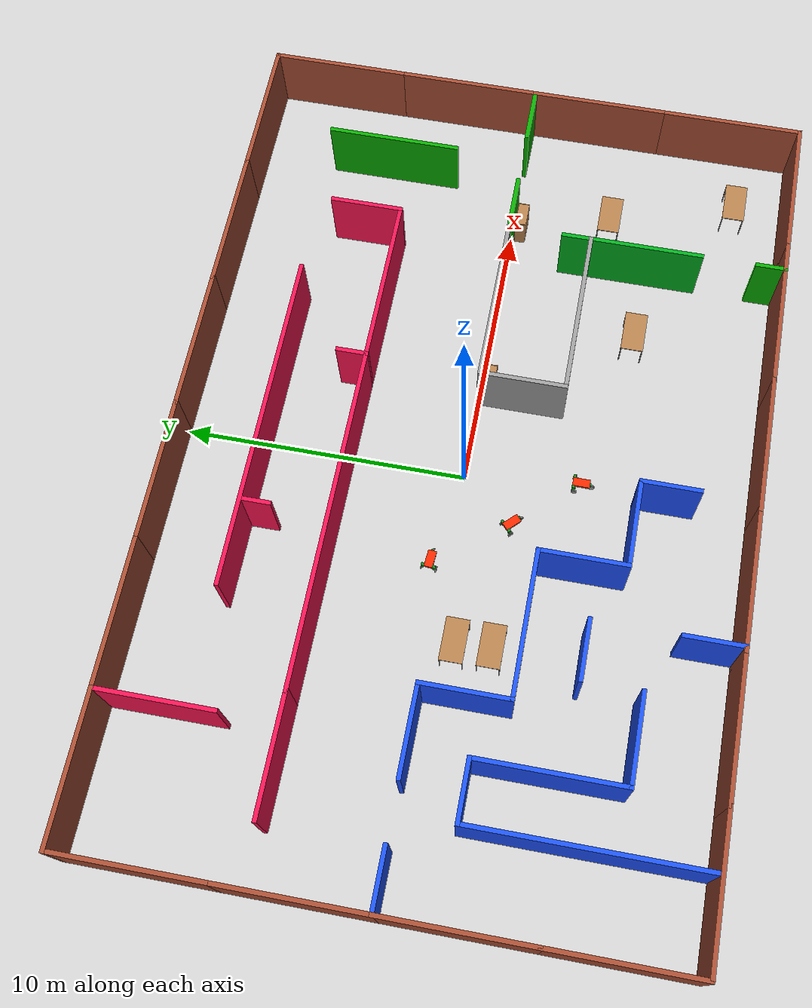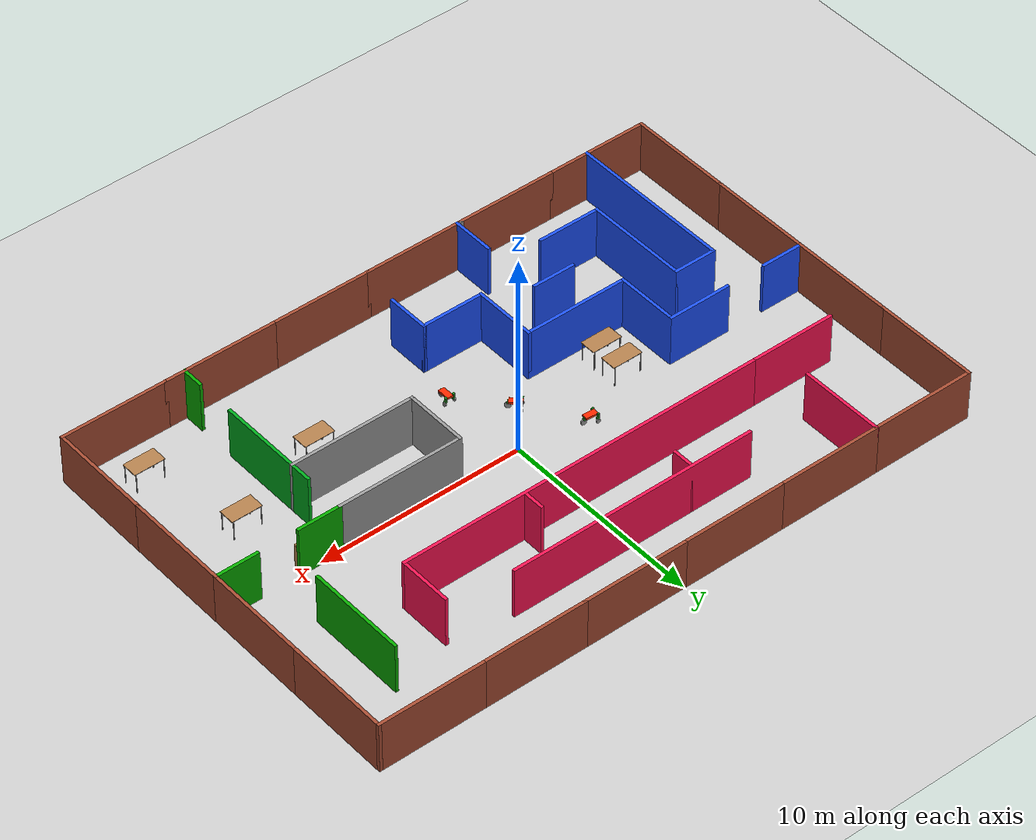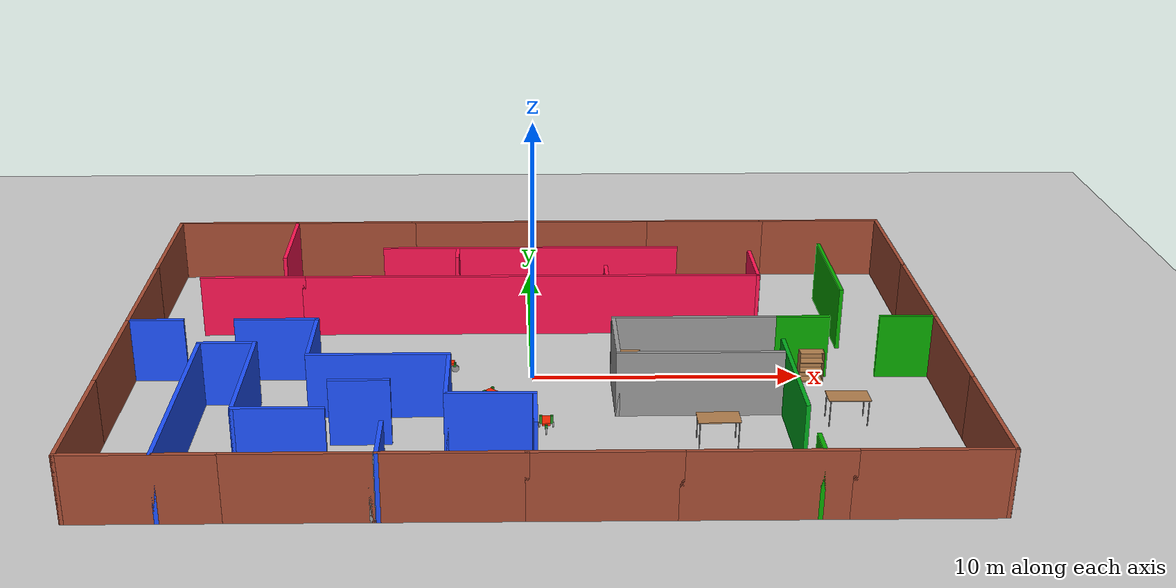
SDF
<sdf version="1.7">
 <world name="default">
  <plugin name="welcome" filename="libwelcome.so"/>
  <light name="sun" type="directional">
   <pose>0 0 10 0 -0 0</pose>
   <diffuse>0.8 0.8 0.8 1</diffuse>
   <specular>0.2 0.2 0.2 1</specular>
   <attenuation>
    <range>1000</range>
    <constant>0.9</constant>
    <linear>0.01</linear>
    <quadratic>0.001</quadratic>
   </attenuation>
   <direction>-0.5 0.1 -0.9</direction>
   <spot><inner_angle>0</inner_angle><outer_angle>0</outer_angle><falloff>0</falloff></spot>
  </light>
  <model name="ground_plane">
   <static>1</static>
   <link name="link">
    <collision name="collision">
     <geometry><plane><normal>0 0 1</normal><size>100 100</size></plane></geometry>
     <surface>
      <contact><collide_bitmask>65535</collide_bitmask></contact>
      <friction><ode><mu>100</mu><mu2>50</mu2></ode></friction>
     </surface>
    </collision>
    <visual name="visual">
     <cast_shadows>0</cast_shadows>
     <geometry><plane><normal>0 0 1</normal><size>100 100</size></plane></geometry>
     <material>
      <script><uri>file://media/materials/scripts/gazebo.material</uri><name>Gazebo/Grey</name></script>
     </material>
    </visual>
   </link>
  </model>
  <gravity>0 0 -9.8</gravity>
  <magnetic_field>6e-06 2.3e-05 -4.2e-05</magnetic_field>
  <atmosphere type="adiabatic"/>
  <physics type="ode">
   <max_step_size>0.001</max_step_size>
   <real_time_factor>1</real_time_factor>
   <real_time_update_rate>1000</real_time_update_rate>
  </physics>
  <scene><ambient>0.4 0.4 0.4 1</ambient><background>0.7 0.7 0.7 1</background><shadows>1</shadows></scene>
  <spherical_coordinates>
   <surface_model>EARTH_WGS84</surface_model>
   <latitude_deg>0</latitude_deg>
   <longitude_deg>0</longitude_deg>
   <elevation>0</elevation>
   <heading_deg>0</heading_deg>
  </spherical_coordinates>
  <model name="Building">
   <link name="Wall_10">
    <collision name="Wall_10_Collision">
     <geometry><box><size>5.15 0.15 2.5</size></box></geometry>
     <pose>0 0 1.25 0 -0 0</pose>
    </collision>
    <visual name="Wall_10_Visual">
     <pose>0 0 1.25 0 -0 0</pose>
     <geometry><box><size>5.15 0.15 2.5</size></box></geometry>
     <material>
      <script><uri>file://media/materials/scripts/gazebo.material</uri><name>Gazebo/Bricks</name></script>
      <ambient>1 1 1 1</ambient>
     </material>
     <meta><layer>0</layer></meta>
    </visual>
    <pose>-12.5 -10 0 0 -0 0</pose>
   </link>
   <link name="Wall_13">
    <collision name="Wall_13_Collision">
     <geometry><box><size>4.97634 0.15 2.5</size></box></geometry>
     <pose>0 0 1.25 0 -0 0</pose>
    </collision>
    <visual name="Wall_13_Visual">
     <pose>0 0 1.25 0 -0 0</pose>
     <geometry><box><size>4.97634 0.15 2.5</size></box></geometry>
     <material>
      <script><uri>file://media/materials/scripts/gazebo.material</uri><name>Gazebo/Bricks</name></script>
      <ambient>1 1 1 1</ambient>
     </material>
     <meta><layer>0</layer></meta>
    </visual>
    <pose>-7.58683 -10 0 0 -0 0</pose>
   </link>
   <link name="Wall_14">
    <collision name="Wall_14_Collision">
     <geometry><box><size>0.207321 0.15 2.5</size></box></geometry>
     <pose>0 0 1.25 0 -0 0</pose>
    </collision>
    <visual name="Wall_14_Visual">
     <pose>0 0 1.25 0 -0 0</pose>
     <geometry><box><size>0.207321 0.15 2.5</size></box></geometry>
     <material>
      <script><uri>file://media/materials/scripts/gazebo.material</uri><name>Gazebo/Grey</name></script>
      <ambient>1 1 1 1</ambient>
     </material>
     <meta><layer>0</layer></meta>
    </visual>
    <pose>-5.16866 -10 0 0 -0 0</pose>
   </link>
   <link name="Wall_15">
    <collision name="Wall_15_Collision">
     <geometry><box><size>5 0.15 2.5</size></box></geometry>
     <pose>0 0 1.25 0 -0 0</pose>
    </collision>
    <visual name="Wall_15_Visual">
     <pose>0 0 1.25 0 -0 0</pose>
     <geometry><box><size>5 0.15 2.5</size></box></geometry>
     <material>
      <script><uri>file://media/materials/scripts/gazebo.material</uri><name>Gazebo/Bricks</name></script>
      <ambient>1 1 1 1</ambient>
     </material>
     <meta><layer>0</layer></meta>
    </visual>
    <pose>-2.715 -10 0 0 -0 0</pose>
   </link>
   <link name="Wall_16">
    <collision name="Wall_16_Collision">
     <geometry><box><size>5 0.15 2.5</size></box></geometry>
     <pose>0 0 1.25 0 -0 0</pose>
    </collision>
    <visual name="Wall_16_Visual">
     <pose>0 0 1.25 0 -0 0</pose>
     <geometry><box><size>5 0.15 2.5</size></box></geometry>
     <material>
      <script><uri>file://media/materials/scripts/gazebo.material</uri><name>Gazebo/Bricks</name></script>
      <ambient>1 1 1 1</ambient>
     </material>
     <meta><layer>0</layer></meta>
    </visual>
    <pose>2.135 -10 0 0 -0 0</pose>
   </link>
   <link name="Wall_17">
    <collision name="Wall_17_Collision">
     <geometry><box><size>5.59 0.15 2.5</size></box></geometry>
     <pose>0 0 1.25 0 -0 0</pose>
    </collision>
    <visual name="Wall_17_Visual">
     <pose>0 0 1.25 0 -0 0</pose>
     <geometry><box><size>5.59 0.15 2.5</size></box></geometry>
     <material>
      <script><uri>file://media/materials/scripts/gazebo.material</uri><name>Gazebo/Bricks</name></script>
      <ambient>1 1 1 1</ambient>
     </material>
     <meta><layer>0</layer></meta>
    </visual>
    <pose>7.28 -10 0 0 -0 0</pose>
   </link>
   <link name="Wall_18">
    <collision name="Wall_18_Collision">
     <geometry><box><size>5.15 0.15 2.5</size></box></geometry>
     <pose>0 0 1.25 0 -0 0</pose>
    </collision>
    <visual name="Wall_18_Visual">
     <pose>0 0 1.25 0 -0 0</pose>
     <geometry><box><size>5.15 0.15 2.5</size></box></geometry>
     <material>
      <script><uri>file://media/materials/scripts/gazebo.material</uri><name>Gazebo/Bricks</name></script>
      <ambient>1 1 1 1</ambient>
     </material>
     <meta><layer>0</layer></meta>
    </visual>
    <pose>12.5 -10 0 0 -0 0</pose>
   </link>
   <link name="Wall_21">
    <collision name="Wall_21_Collision">
     <geometry><box><size>5.15 0.15 2.5</size></box></geometry>
     <pose>0 0 1.25 0 -0 0</pose>
    </collision>
    <visual name="Wall_21_Visual">
     <pose>0 0 1.25 0 -0 0</pose>
     <geometry><box><size>5.15 0.15 2.5</size></box></geometry>
     <material>
      <script><uri>file://media/materials/scripts/gazebo.material</uri><name>Gazebo/Bricks</name></script>
      <ambient>1 1 1 1</ambient>
     </material>
     <meta><layer>0</layer></meta>
    </visual>
    <pose>15 -7.5 0 0 -0 1.5708</pose>
   </link>
   <link name="Wall_22">
    <collision name="Wall_22_Collision">
     <geometry><box><size>5.15 0.15 2.5</size></box></geometry>
     <pose>0 0 1.25 0 -0 0</pose>
    </collision>
    <visual name="Wall_22_Visual">
     <pose>0 0 1.25 0 -0 0</pose>
     <geometry><box><size>5.15 0.15 2.5</size></box></geometry>
     <material>
      <script><uri>file://media/materials/scripts/gazebo.material</uri><name>Gazebo/Bricks</name></script>
      <ambient>1 1 1 1</ambient>
     </material>
     <meta><layer>0</layer></meta>
    </visual>
    <pose>15 -2.5 0 0 -0 1.5708</pose>
   </link>
   <link name="Wall_23">
    <collision name="Wall_23_Collision">
     <geometry><box><size>5.15 0.15 2.5</size></box></geometry>
     <pose>0 0 1.25 0 -0 0</pose>
    </collision>
    <visual name="Wall_23_Visual">
     <pose>0 0 1.25 0 -0 0</pose>
     <geometry><box><size>5.15 0.15 2.5</size></box></geometry>
     <material>
      <script><uri>file://media/materials/scripts/gazebo.material</uri><name>Gazebo/Bricks</name></script>
      <ambient>1 1 1 1</ambient>
     </material>
     <meta><layer>0</layer></meta>
    </visual>
    <pose>15 2.5 0 0 -0 1.5708</pose>
   </link>
   <link name="Wall_24">
    <collision name="Wall_24_Collision">
     <geometry><box><size>5.15 0.15 2.5</size></box></geometry>
     <pose>0 0 1.25 0 -0 0</pose>
    </collision>
    <visual name="Wall_24_Visual">
     <pose>0 0 1.25 0 -0 0</pose>
     <geometry><box><size>5.15 0.15 2.5</size></box></geometry>
     <material>
      <script><uri>file://media/materials/scripts/gazebo.material</uri><name>Gazebo/Bricks</name></script>
      <ambient>1 1 1 1</ambient>
     </material>
     <meta><layer>0</layer></meta>
    </visual>
    <pose>15 7.5 0 0 -0 1.5708</pose>
   </link>
   <link name="Wall_25">
    <collision name="Wall_25_Collision">
     <geometry><box><size>5.15 0.15 2.5</size></box></geometry>
     <pose>0 0 1.25 0 -0 0</pose>
    </collision>
    <visual name="Wall_25_Visual">
     <pose>0 0 1.25 0 -0 0</pose>
     <geometry><box><size>5.15 0.15 2.5</size></box></geometry>
     <material>
      <script><uri>file://media/materials/scripts/gazebo.material</uri><name>Gazebo/Bricks</name></script>
      <ambient>1 1 1 1</ambient>
     </material>
     <meta><layer>0</layer></meta>
    </visual>
    <pose>12.5 10 0 0 -0 3.14159</pose>
   </link>
   <link name="Wall_26">
    <collision name="Wall_26_Collision">
     <geometry><box><size>5.15 0.15 2.5</size></box></geometry>
     <pose>0 0 1.25 0 -0 0</pose>
    </collision>
    <visual name="Wall_26_Visual">
     <pose>0 0 1.25 0 -0 0</pose>
     <geometry><box><size>5.15 0.15 2.5</size></box></geometry>
     <material>
      <script><uri>file://media/materials/scripts/gazebo.material</uri><name>Gazebo/Bricks</name></script>
      <ambient>1 1 1 1</ambient>
     </material>
     <meta><layer>0</layer></meta>
    </visual>
    <pose>7.5 10 0 0 -0 3.14159</pose>
   </link>
   <link name="Wall_28">
    <collision name="Wall_28_Collision">
     <geometry><box><size>5.15 0.15 2.5</size></box></geometry>
     <pose>0 0 1.25 0 -0 0</pose>
    </collision>
    <visual name="Wall_28_Visual">
     <pose>0 0 1.25 0 -0 0</pose>
     <geometry><box><size>5.15 0.15 2.5</size></box></geometry>
     <material>
      <script><uri>file://media/materials/scripts/gazebo.material</uri><name>Gazebo/Bricks</name></script>
      <ambient>1 1 1 1</ambient>
     </material>
     <meta><layer>0</layer></meta>
    </visual>
    <pose>2.5 10 0 0 -0 3.14159</pose>
   </link>
   <link name="Wall_29">
    <collision name="Wall_29_Collision">
     <geometry><box><size>5.15 0.15 2.5</size></box></geometry>
     <pose>0 0 1.25 0 -0 0</pose>
    </collision>
    <visual name="Wall_29_Visual">
     <pose>0 0 1.25 0 -0 0</pose>
     <geometry><box><size>5.15 0.15 2.5</size></box></geometry>
     <material>
      <script><uri>file://media/materials/scripts/gazebo.material</uri><name>Gazebo/Bricks</name></script>
      <ambient>1 1 1 1</ambient>
     </material>
     <meta><layer>0</layer></meta>
    </visual>
    <pose>-2.5 10 0 0 -0 3.14159</pose>
   </link>
   <link name="Wall_31">
    <collision name="Wall_31_Collision">
     <geometry><box><size>5.15 0.15 2.5</size></box></geometry>
     <pose>0 0 1.25 0 -0 0</pose>
    </collision>
    <visual name="Wall_31_Visual">
     <pose>0 0 1.25 0 -0 0</pose>
     <geometry><box><size>5.15 0.15 2.5</size></box></geometry>
     <material>
      <script><uri>file://media/materials/scripts/gazebo.material</uri><name>Gazebo/Bricks</name></script>
      <ambient>1 1 1 1</ambient>
     </material>
     <meta><layer>0</layer></meta>
    </visual>
    <pose>-12.5 10 0 0 -0 3.14159</pose>
   </link>
   <link name="Wall_32">
    <collision name="Wall_32_Collision">
     <geometry><box><size>5.15 0.15 2.5</size></box></geometry>
     <pose>0 0 1.25 0 -0 0</pose>
    </collision>
    <visual name="Wall_32_Visual">
     <pose>0 0 1.25 0 -0 0</pose>
     <geometry><box><size>5.15 0.15 2.5</size></box></geometry>
     <material>
      <script><uri>file://media/materials/scripts/gazebo.material</uri><name>Gazebo/Bricks</name></script>
      <ambient>1 1 1 1</ambient>
     </material>
     <meta><layer>0</layer></meta>
    </visual>
    <pose>-15 7.5 0 0 -0 -1.5708</pose>
   </link>
   <link name="Wall_33">
    <collision name="Wall_33_Collision">
     <geometry><box><size>5.15 0.15 2.5</size></box></geometry>
     <pose>0 0 1.25 0 -0 0</pose>
    </collision>
    <visual name="Wall_33_Visual">
     <pose>0 0 1.25 0 -0 0</pose>
     <geometry><box><size>5.15 0.15 2.5</size></box></geometry>
     <material>
      <script><uri>file://media/materials/scripts/gazebo.material</uri><name>Gazebo/Bricks</name></script>
      <ambient>1 1 1 1</ambient>
     </material>
     <meta><layer>0</layer></meta>
    </visual>
    <pose>-15 2.5 0 0 -0 -1.5708</pose>
   </link>
   <link name="Wall_34">
    <collision name="Wall_34_Collision">
     <geometry><box><size>5.15 0.15 2.5</size></box></geometry>
     <pose>0 0 1.25 0 -0 0</pose>
    </collision>
    <visual name="Wall_34_Visual">
     <pose>0 0 1.25 0 -0 0</pose>
     <geometry><box><size>5.15 0.15 2.5</size></box></geometry>
     <material>
      <script><uri>file://media/materials/scripts/gazebo.material</uri><name>Gazebo/Bricks</name></script>
      <ambient>1 1 1 1</ambient>
     </material>
     <meta><layer>0</layer></meta>
    </visual>
    <pose>-15 -2.5 0 0 -0 -1.5708</pose>
   </link>
   <link name="Wall_35">
    <collision name="Wall_35_Collision">
     <geometry><box><size>5.15 0.15 2.5</size></box></geometry>
     <pose>0 0 1.25 0 -0 0</pose>
    </collision>
    <visual name="Wall_35_Visual">
     <pose>0 0 1.25 0 -0 0</pose>
     <geometry><box><size>5.15 0.15 2.5</size></box></geometry>
     <material>
      <script><uri>file://media/materials/scripts/gazebo.material</uri><name>Gazebo/Bricks</name></script>
      <ambient>1 1 1 1</ambient>
     </material>
     <meta><layer>0</layer></meta>
    </visual>
    <pose>-15 -7.5 0 0 -0 -1.5708</pose>
   </link>
   <link name="Wall_37">
    <collision name="Wall_37_Collision">
     <geometry><box><size>5.15 0.15 2.5</size></box></geometry>
     <pose>0 0 1.25 0 -0 0</pose>
    </collision>
    <visual name="Wall_37_Visual">
     <pose>0 0 1.25 0 -0 0</pose>
     <geometry><box><size>5.15 0.15 2.5</size></box></geometry>
     <material>
      <script><uri>file://media/materials/scripts/gazebo.material</uri><name>Gazebo/Bricks</name></script>
      <ambient>1 1 1 1</ambient>
     </material>
     <meta><layer>0</layer></meta>
    </visual>
    <pose>-7.5 10 0 0 -0 0</pose>
   </link>
   <link name="Wall_39">
    <collision name="Wall_39_Collision">
     <geometry><box><size>8.15 0.15 2.5</size></box></geometry>
     <pose>0 0 1.25 0 -0 0</pose>
    </collision>
    <visual name="Wall_39_Visual">
     <pose>0 0 1.25 0 -0 0</pose>
     <geometry><box><size>8.15 0.15 2.5</size></box></geometry>
     <material>
      <script><uri>file://media/materials/scripts/gazebo.material</uri><name>Gazebo/Grey</name></script>
      <ambient>0.113725 0.321569 1 1</ambient>
     </material>
     <meta><layer>0</layer></meta>
    </visual>
    <pose>-12 -6 0 0 -0 1.5708</pose>
   </link>
   <link name="Wall_41">
    <collision name="Wall_41_Collision">
     <geometry><box><size>2.15 0.15 2.5</size></box></geometry>
     <pose>0 0 1.25 0 -0 0</pose>
    </collision>
    <visual name="Wall_41_Visual">
     <pose>0 0 1.25 0 -0 0</pose>
     <geometry><box><size>2.15 0.15 2.5</size></box></geometry>
     <material>
      <script><uri>file://media/materials/scripts/gazebo.material</uri><name>Gazebo/Grey</name></script>
      <ambient>0.113725 0.321569 1 1</ambient>
     </material>
     <meta><layer>0</layer></meta>
    </visual>
    <pose>-14 0 0 0 -0 0</pose>
   </link>
   <link name="Wall_43">
    <collision name="Wall_43_Collision">
     <geometry><box><size>5.15 0.15 2.5</size></box></geometry>
     <pose>0 0 1.25 0 -0 0</pose>
    </collision>
    <visual name="Wall_43_Visual">
     <pose>0 0 1.25 0 -0 0</pose>
     <geometry><box><size>5.15 0.15 2.5</size></box></geometry>
     <material>
      <script><uri>file://media/materials/scripts/gazebo.material</uri><name>Gazebo/Grey</name></script>
      <ambient>0.113725 0.321569 1 1</ambient>
     </material>
     <meta><layer>0</layer></meta>
    </visual>
    <pose>-5.5 -3 0 0 -0 0</pose>
   </link>
   <link name="Wall_44">
    <collision name="Wall_44_Collision">
     <geometry><box><size>3.15 0.15 2.5</size></box></geometry>
     <pose>0 0 1.25 0 -0 0</pose>
    </collision>
    <visual name="Wall_44_Visual">
     <pose>0 0 1.25 0 -0 0</pose>
     <geometry><box><size>3.15 0.15 2.5</size></box></geometry>
     <material>
      <script><uri>file://media/materials/scripts/gazebo.material</uri><name>Gazebo/Grey</name></script>
      <ambient>0.113725 0.321569 1 1</ambient>
     </material>
     <meta><layer>0</layer></meta>
    </visual>
    <pose>-3 -4.5 0 0 -0 -1.5708</pose>
   </link>
   <link name="Wall_45">
    <collision name="Wall_45_Collision">
     <geometry><box><size>3.15 0.15 2.5</size></box></geometry>
     <pose>0 0 1.25 0 -0 0</pose>
    </collision>
    <visual name="Wall_45_Visual">
     <pose>0 0 1.25 0 -0 0</pose>
     <geometry><box><size>3.15 0.15 2.5</size></box></geometry>
     <material>
      <script><uri>file://media/materials/scripts/gazebo.material</uri><name>Gazebo/Grey</name></script>
      <ambient>0.113725 0.321569 1 1</ambient>
     </material>
     <meta><layer>0</layer></meta>
    </visual>
    <pose>-1.5 -6 0 0 -0 0</pose>
   </link>
   <link name="Wall_46">
    <collision name="Wall_46_Collision">
     <geometry><box><size>2.15 0.15 2.5</size></box></geometry>
     <pose>0 0 1.25 0 -0 0</pose>
    </collision>
    <visual name="Wall_46_Visual">
     <pose>0 0 1.25 0 -0 0</pose>
     <geometry><box><size>2.15 0.15 2.5</size></box></geometry>
     <material>
      <script><uri>file://media/materials/scripts/gazebo.material</uri><name>Gazebo/Grey</name></script>
      <ambient>0.113725 0.321569 1 1</ambient>
     </material>
     <meta><layer>0</layer></meta>
    </visual>
    <pose>0 -7 0 0 -0 -1.5708</pose>
   </link>
   <link name="Wall_48">
    <collision name="Wall_48_Collision">
     <geometry><box><size>2.15 0.15 2.5</size></box></geometry>
     <pose>0 0 1.25 0 -0 0</pose>
    </collision>
    <visual name="Wall_48_Visual">
     <pose>0 0 1.25 0 -0 0</pose>
     <geometry><box><size>2.15 0.15 2.5</size></box></geometry>
     <material>
      <script><uri>file://media/materials/scripts/gazebo.material</uri><name>Gazebo/Grey</name></script>
      <ambient>0.113725 0.321569 1 1</ambient>
     </material>
     <meta><layer>0</layer></meta>
    </visual>
    <pose>-11 -2 0 0 -0 0</pose>
   </link>
   <link name="Wall_49">
    <collision name="Wall_49_Collision">
     <geometry><box><size>5.15 0.15 2.5</size></box></geometry>
     <pose>0 0 1.25 0 -0 0</pose>
    </collision>
    <visual name="Wall_49_Visual">
     <pose>0 0 1.25 0 -0 0</pose>
     <geometry><box><size>5.15 0.15 2.5</size></box></geometry>
     <material>
      <script><uri>file://media/materials/scripts/gazebo.material</uri><name>Gazebo/Grey</name></script>
      <ambient>0.113725 0.321569 1 1</ambient>
     </material>
     <meta><layer>0</layer></meta>
    </visual>
    <pose>-10 -4.5 0 0 -0 -1.5708</pose>
   </link>
   <link name="Wall_50">
    <collision name="Wall_50_Collision">
     <geometry><box><size>3.15 0.15 2.5</size></box></geometry>
     <pose>0 0 1.25 0 -0 0</pose>
    </collision>
    <visual name="Wall_50_Visual">
     <pose>0 0 1.25 0 -0 0</pose>
     <geometry><box><size>3.15 0.15 2.5</size></box></geometry>
     <material>
      <script><uri>file://media/materials/scripts/gazebo.material</uri><name>Gazebo/Grey</name></script>
      <ambient>0.113725 0.321569 1 1</ambient>
     </material>
     <meta><layer>0</layer></meta>
    </visual>
    <pose>-8.5 -7 0 0 -0 0</pose>
   </link>
   <link name="Wall_52">
    <collision name="Wall_52_Collision">
     <geometry><box><size>2.15 0.15 2.5</size></box></geometry>
     <pose>0 0 1.25 0 -0 0</pose>
    </collision>
    <visual name="Wall_52_Visual">
     <pose>0 0 1.25 0 -0 0</pose>
     <geometry><box><size>2.15 0.15 2.5</size></box></geometry>
     <material>
      <script><uri>file://media/materials/scripts/gazebo.material</uri><name>Gazebo/Grey</name></script>
      <ambient>0.113725 0.321569 1 1</ambient>
     </material>
     <meta><layer>0</layer></meta>
    </visual>
    <pose>-6 -5 0 0 -0 0</pose>
   </link>
   <link name="Wall_54">
    <collision name="Wall_54_Collision">
     <geometry><box><size>2.15 0.15 2.5</size></box></geometry>
     <pose>0 0 1.25 0 -0 0</pose>
    </collision>
    <visual name="Wall_54_Visual">
     <pose>0 0 1.25 0 -0 0</pose>
     <geometry><box><size>2.15 0.15 2.5</size></box></geometry>
     <material>
      <script><uri>file://media/materials/scripts/gazebo.material</uri><name>Gazebo/Grey</name></script>
      <ambient>0.113725 0.321569 1 1</ambient>
     </material>
     <meta><layer>0</layer></meta>
    </visual>
    <pose>-5 -9 0 0 -0 -1.5708</pose>
   </link>
   <link name="Wall_56">
    <collision name="Wall_56_Collision">
     <geometry><box><size>3.15 0.15 2.5</size></box></geometry>
     <pose>0 0 1.25 0 -0 0</pose>
    </collision>
    <visual name="Wall_56_Visual">
     <pose>0 0 1.25 0 -0 0</pose>
     <geometry><box><size>3.15 0.15 2.5</size></box></geometry>
     <material>
      <script><uri>file://media/materials/scripts/gazebo.material</uri><name>Gazebo/Grey</name></script>
      <ambient>0.113725 0.321569 1 1</ambient>
     </material>
     <meta><layer>0</layer></meta>
    </visual>
    <pose>-9.5 0 0 0 -0 0</pose>
   </link>
   <link name="Wall_57">
    <collision name="Wall_57_Collision">
     <geometry><box><size>3.15 0.15 2.5</size></box></geometry>
     <pose>0 0 1.25 0 -0 0</pose>
    </collision>
    <visual name="Wall_57_Visual">
     <pose>0 0 1.25 0 -0 0</pose>
     <geometry><box><size>3.15 0.15 2.5</size></box></geometry>
     <material>
      <script><uri>file://media/materials/scripts/gazebo.material</uri><name>Gazebo/Grey</name></script>
      <ambient>0.113725 0.321569 1 1</ambient>
     </material>
     <meta><layer>0</layer></meta>
    </visual>
    <pose>-8 -1.5 0 0 -0 -1.5708</pose>
   </link>
   <link name="Wall_59">
    <collision name="Wall_59_Collision">
     <geometry><box><size>1.15 0.15 2.5</size></box></geometry>
     <pose>0 0 1.25 0 -0 0</pose>
    </collision>
    <visual name="Wall_59_Visual">
     <pose>0 0 1.25 0 -0 0</pose>
     <geometry><box><size>1.15 0.15 2.5</size></box></geometry>
     <material>
      <script><uri>file://media/materials/scripts/gazebo.material</uri><name>Gazebo/Grey</name></script>
      <ambient>0.0313726 0.666667 0 1</ambient>
     </material>
     <meta><layer>0</layer></meta>
    </visual>
    <pose>9 -9.5 0 0 -0 1.5708</pose>
   </link>
   <link name="Wall_62">
    <collision name="Wall_62_Collision">
     <geometry><box><size>5.15 0.15 2.5</size></box></geometry>
     <pose>0 0 1.25 0 -0 0</pose>
    </collision>
    <visual name="Wall_62_Visual">
     <pose>0 0 1.25 0 -0 0</pose>
     <geometry><box><size>5.15 0.15 2.5</size></box></geometry>
     <material>
      <script><uri>file://media/materials/scripts/gazebo.material</uri><name>Gazebo/Grey</name></script>
      <ambient>0 0.666667 0.109804 1</ambient>
     </material>
     <meta><layer>0</layer></meta>
    </visual>
    <pose>9 -4.5 0 0 -0 1.5708</pose>
   </link>
   <link name="Wall_63">
    <collision name="Wall_63_Collision">
     <geometry><box><size>2.15 0.15 2.5</size></box></geometry>
     <pose>0 0 1.25 0 -0 0</pose>
    </collision>
    <visual name="Wall_63_Visual">
     <pose>0 0 1.25 0 -0 0</pose>
     <geometry><box><size>2.15 0.15 2.5</size></box></geometry>
     <material>
      <script><uri>file://media/materials/scripts/gazebo.material</uri><name>Gazebo/Grey</name></script>
      <ambient>0.0313726 0.666667 0 1</ambient>
     </material>
     <meta><layer>0</layer></meta>
    </visual>
    <pose>10 0 0 0 -0 0</pose>
   </link>
   <link name="Wall_65">
    <collision name="Wall_65_Collision">
     <geometry><box><size>2.15 0.15 2.5</size></box></geometry>
     <pose>0 0 1.25 0 -0 0</pose>
    </collision>
    <visual name="Wall_65_Visual">
     <pose>0 0 1.25 0 -0 0</pose>
     <geometry><box><size>2.15 0.15 2.5</size></box></geometry>
     <material>
      <script><uri>file://media/materials/scripts/gazebo.material</uri><name>Gazebo/Grey</name></script>
      <ambient>0.0313726 0.666667 0 1</ambient>
     </material>
     <meta><layer>0</layer></meta>
    </visual>
    <pose>14 0 0 0 -0 0</pose>
   </link>
   <link name="Wall_68">
    <collision name="Wall_68_Collision">
     <geometry><box><size>4.15 0.15 2.5</size></box></geometry>
     <pose>0 0 1.25 0 -0 0</pose>
    </collision>
    <visual name="Wall_68_Visual">
     <pose>0 0 1.25 0 -0 0</pose>
     <geometry><box><size>4.15 0.15 2.5</size></box></geometry>
     <material>
      <script><uri>file://media/materials/scripts/gazebo.material</uri><name>Gazebo/Grey</name></script>
      <ambient>1 0.0745098 0.321569 1</ambient>
     </material>
     <meta><layer>0</layer></meta>
    </visual>
    <pose>-10 8 0 0 -0 1.5708</pose>
   </link>
   <link name="Wall_70">
    <collision name="Wall_70_Collision">
     <geometry><box><size>4.15 0.15 2.5</size></box></geometry>
     <pose>0 0 1.25 0 -0 0</pose>
    </collision>
    <visual name="Wall_70_Visual">
     <pose>0 0 1.25 0 -0 0</pose>
     <geometry><box><size>4.15 0.15 2.5</size></box></geometry>
     <material>
      <script><uri>file://media/materials/scripts/gazebo.material</uri><name>Gazebo/Grey</name></script>
      <ambient>1 0.0745098 0.321569 1</ambient>
     </material>
     <meta><layer>0</layer></meta>
    </visual>
    <pose>-11 4 0 0 -0 0</pose>
   </link>
   <link name="Wall_72">
    <collision name="Wall_72_Collision">
     <geometry><box><size>12.15 0.15 2.5</size></box></geometry>
     <pose>0 0 1.25 0 -0 0</pose>
    </collision>
    <visual name="Wall_72_Visual">
     <pose>0 0 1.25 0 -0 0</pose>
     <geometry><box><size>12.15 0.15 2.5</size></box></geometry>
     <material>
      <script><uri>file://media/materials/scripts/gazebo.material</uri><name>Gazebo/Grey</name></script>
      <ambient>1 0.0745098 0.321569 1</ambient>
     </material>
     <meta><layer>0</layer></meta>
    </visual>
    <pose>0 7 0 0 -0 0</pose>
   </link>
   <link name="Wall_75">
    <collision name="Wall_75_Collision">
     <geometry><box><size>18.15 0.15 2.5</size></box></geometry>
     <pose>0 0 1.25 0 -0 0</pose>
    </collision>
    <visual name="Wall_75_Visual">
     <pose>0 0 1.25 0 -0 0</pose>
     <geometry><box><size>18.15 0.15 2.5</size></box></geometry>
     <material>
      <script><uri>file://media/materials/scripts/gazebo.material</uri><name>Gazebo/Grey</name></script>
      <ambient>1 0.0745098 0.321569 1</ambient>
     </material>
     <meta><layer>0</layer></meta>
    </visual>
    <pose>0 4 0 0 -0 0</pose>
   </link>
   <link name="Wall_77">
    <collision name="Wall_77_Collision">
     <geometry><box><size>1.15 0.15 2.5</size></box></geometry>
     <pose>0 0 1.25 0 -0 0</pose>
    </collision>
    <visual name="Wall_77_Visual">
     <pose>0 0 1.25 0 -0 0</pose>
     <geometry><box><size>1.15 0.15 2.5</size></box></geometry>
     <material>
      <script><uri>file://media/materials/scripts/gazebo.material</uri><name>Gazebo/Grey</name></script>
      <ambient>1 0.0745098 0.321569 1</ambient>
     </material>
     <meta><layer>0</layer></meta>
    </visual>
    <pose>-3 6.5 0 0 -0 -1.5708</pose>
   </link>
   <link name="Wall_79">
    <collision name="Wall_79_Collision">
     <geometry><box><size>1.15 0.15 2.5</size></box></geometry>
     <pose>0 0 1.25 0 -0 0</pose>
    </collision>
    <visual name="Wall_79_Visual">
     <pose>0 0 1.25 0 -0 0</pose>
     <geometry><box><size>1.15 0.15 2.5</size></box></geometry>
     <material>
      <script><uri>file://media/materials/scripts/gazebo.material</uri><name>Gazebo/Grey</name></script>
      <ambient>1 0.0745098 0.321569 1</ambient>
     </material>
     <meta><layer>0</layer></meta>
    </visual>
    <pose>3 4.5 0 0 -0 1.5708</pose>
   </link>
   <link name="Wall_81">
    <collision name="Wall_81_Collision">
     <geometry><box><size>2.65 0.15 2.5</size></box></geometry>
     <pose>0 0 1.25 0 -0 0</pose>
    </collision>
    <visual name="Wall_81_Visual">
     <pose>0 0 1.25 0 -0 0</pose>
     <geometry><box><size>2.65 0.15 2.5</size></box></geometry>
     <material>
      <script><uri>file://media/materials/scripts/gazebo.material</uri><name>Gazebo/Grey</name></script>
      <ambient>1 0.0745098 0.321569 1</ambient>
     </material>
     <meta><layer>0</layer></meta>
    </visual>
    <pose>9 5.25 0 0 -0 -1.5708</pose>
   </link>
   <link name="Wall_83">
    <collision name="Wall_83_Collision">
     <geometry><box><size>4.85 0.15 2.5</size></box></geometry>
     <pose>0 0 1.25 0 -0 0</pose>
    </collision>
    <visual name="Wall_83_Visual">
     <pose>0 0 1.25 0 -0 0</pose>
     <geometry><box><size>4.85 0.15 2.5</size></box></geometry>
     <material>
      <script><uri>file://media/materials/scripts/gazebo.material</uri><name>Gazebo/Grey</name></script>
      <ambient>0.0313726 0.666667 0 1</ambient>
     </material>
     <meta><layer>0</layer></meta>
    </visual>
    <pose>12 4.85 0 0 -0 -1.5708</pose>
   </link>
   <link name="Wall_85">
    <collision name="Wall_85_Collision">
     <geometry><box><size>6.15 0.15 2.5</size></box></geometry>
     <pose>0 0 1.25 0 -0 0</pose>
    </collision>
    <visual name="Wall_85_Visual">
     <pose>0 0 1.25 0 -0 0</pose>
     <geometry><box><size>6.15 0.15 2.5</size></box></geometry>
     <material>
      <script><uri>file://media/materials/scripts/gazebo.material</uri><name>Gazebo/Grey</name></script>
      <ambient>1 1 1 1</ambient>
     </material>
     <meta><layer>0</layer></meta>
    </visual>
    <pose>6 0 0 0 -0 3.14159</pose>
   </link>
   <link name="Wall_86">
    <collision name="Wall_86_Collision">
     <geometry><box><size>3.15 0.15 2.5</size></box></geometry>
     <pose>0 0 1.25 0 -0 0</pose>
    </collision>
    <visual name="Wall_86_Visual">
     <pose>0 0 1.25 0 -0 0</pose>
     <geometry><box><size>3.15 0.15 2.5</size></box></geometry>
     <material>
      <script><uri>file://media/materials/scripts/gazebo.material</uri><name>Gazebo/Grey</name></script>
      <ambient>1 1 1 1</ambient>
     </material>
     <meta><layer>0</layer></meta>
    </visual>
    <pose>3 -1.5 0 0 -0 -1.5708</pose>
   </link>
   <link name="Wall_87">
    <collision name="Wall_87_Collision">
     <geometry><box><size>6.15 0.15 2.5</size></box></geometry>
     <pose>0 0 1.25 0 -0 0</pose>
    </collision>
    <visual name="Wall_87_Visual">
     <pose>0 0 1.25 0 -0 0</pose>
     <geometry><box><size>6.15 0.15 2.5</size></box></geometry>
     <material>
      <script><uri>file://media/materials/scripts/gazebo.material</uri><name>Gazebo/Grey</name></script>
      <ambient>1 1 1 1</ambient>
     </material>
     <meta><layer>0</layer></meta>
    </visual>
    <pose>6 -3 0 0 -0 0</pose>
   </link>
   <static>1</static>
  </model>
  <light name="user_point_light_0" type="point">
   <pose>-0.162267 0.347591 1 0 -0 0</pose>
   <diffuse>0.5 0.5 0.5 1</diffuse>
   <specular>0.1 0.1 0.1 1</specular>
   <attenuation>
    <range>20</range>
    <constant>0.5</constant>
    <linear>0.01</linear>
    <quadratic>0.001</quadratic>
   </attenuation>
   <cast_shadows>0</cast_shadows>
   <direction>0 0 -1</direction>
   <spot><inner_angle>0</inner_angle><outer_angle>0</outer_angle><falloff>0</falloff></spot>
  </light>
  <model name="Three-Wheels-Robot_0">
   <link name="link_0">
    <inertial>
     <mass>1</mass>
     <inertia>
      <ixx>0.166667</ixx>
      <ixy>0</ixy>
      <ixz>0</ixz>
      <iyy>0.166667</iyy>
      <iyz>0</iyz>
      <izz>0.166667</izz>
     </inertia>
    </inertial>
    <pose>0.05 0 0.195 0 -0 0</pose>
    <visual name="visual">
     <pose>0 0 0 0 0.1 0</pose>
     <geometry><box><size>0.6 0.3 0.1</size></box></geometry>
     <material>
      <lighting>1</lighting>
      <script><uri>file://media/materials/scripts/gazebo.material</uri><name>Gazebo/Grey</name></script>
      <shader type="pixel"><normal_map>__default__</normal_map></shader>
      <ambient>1 0.16 0 1</ambient>
      <diffuse>0.7 0.7 0.7 1</diffuse>
      <specular>0.01 0.01 0.01 1</specular>
      <emissive>0 0 0 1</emissive>
     </material>
    </visual>
    <visual name="ModelPreview_0::link_0::visual_2">
     <pose>-0.25 -0.2 -0.05 0 -0 0</pose>
     <geometry><box><size>0.1 0.1 0.3</size></box></geometry>
     <material>
      <lighting>1</lighting>
      <script><uri>file://media/materials/scripts/gazebo.material</uri><name>Gazebo/Grey</name></script>
      <shader type="pixel"><normal_map>__default__</normal_map></shader>
      <ambient>0.13 0.54 0.13 1</ambient>
      <diffuse>0.7 0.7 0.7 1</diffuse>
      <specular>0.01 0.01 0.01 1</specular>
      <emissive>0 0 0 1</emissive>
     </material>
    </visual>
    <visual name="ModelPreview_0::link_0::visual_3">
     <pose>0.3 0 -0.1 0 -0 0</pose>
     <geometry><box><size>0.1 0.1 0.15</size></box></geometry>
     <material>
      <lighting>1</lighting>
      <script><uri>file://media/materials/scripts/gazebo.material</uri><name>Gazebo/Grey</name></script>
      <shader type="pixel"><normal_map>__default__</normal_map></shader>
      <ambient>0.13 0.54 0.13 1</ambient>
      <diffuse>0.7 0.7 0.7 1</diffuse>
      <specular>0.01 0.01 0.01 1</specular>
      <emissive>0 0 0 1</emissive>
     </material>
    </visual>
    <visual name="ModelPreview_0::link_0::visual_1">
     <pose>-0.25 0.2 -0.05 0 -0 0</pose>
     <geometry><box><size>0.1 0.1 0.3</size></box></geometry>
     <material>
      <lighting>1</lighting>
      <script><uri>file://media/materials/scripts/gazebo.material</uri><name>Gazebo/Grey</name></script>
      <shader type="pixel"><normal_map>__default__</normal_map></shader>
      <ambient>0.13 0.54 0.13 1</ambient>
      <diffuse>0.7 0.7 0.7 1</diffuse>
      <specular>0.01 0.01 0.01 1</specular>
      <emissive>0 0 0 1</emissive>
     </material>
    </visual>
    <collision name="collision">
     <pose>0 0 -0.1 0 -0 0</pose>
     <geometry><box><size>0.65 0.6 0.35</size></box></geometry>
     <surface>
      <friction>
       <ode><mu>1</mu><mu2>1</mu2><fdir1>0 0 0</fdir1><slip1>0</slip1><slip2>0</slip2></ode>
       <torsional>
        <coefficient>1</coefficient>
        <patch_radius>0</patch_radius>
        <surface_radius>0</surface_radius>
        <use_patch_radius>1</use_patch_radius>
        <ode><slip>0</slip></ode>
       </torsional>
      </friction>
      <bounce><restitution_coefficient>0</restitution_coefficient><threshold>1e+06</threshold></bounce>
      <contact>
       <collide_without_contact>0</collide_without_contact>
       <collide_without_contact_bitmask>1</collide_without_contact_bitmask>
       <collide_bitmask>1</collide_bitmask>
       <ode>
        <soft_cfm>0</soft_cfm>
        <soft_erp>0.2</soft_erp>
        <kp>1e+13</kp>
        <kd>1</kd>
        <max_vel>0.01</max_vel>
        <min_depth>0</min_depth>
       </ode>
       <bullet>
        <split_impulse>1</split_impulse>
        <split_impulse_penetration_threshold>-0.01</split_impulse_penetration_threshold>
        <soft_cfm>0</soft_cfm>
        <soft_erp>0.2</soft_erp>
        <kp>1e+13</kp>
        <kd>1</kd>
       </bullet>
      </contact>
     </surface>
    </collision>
   </link>
   <link name="link_2">
    <inertial>
     <mass>1</mass>
     <inertia><ixx>0.145833</ixx><ixy>0</ixy><ixz>0</ixz><iyy>0.145833</iyy><iyz>0</iyz><izz>0.125</izz></inertia>
    </inertial>
    <pose>-0.2 -0.25 -0.055 0 -0 0</pose>
    <visual name="visual">
     <pose>0 0 0 1.5707 -0 0</pose>
     <geometry><cylinder><radius>0.1</radius><length>0.05</length></cylinder></geometry>
     <material>
      <lighting>1</lighting>
      <script><uri>file://media/materials/scripts/gazebo.material</uri><name>Gazebo/Grey</name></script>
      <shader type="pixel"><normal_map>__default__</normal_map></shader>
      <ambient>0.3 0.3 0.3 1</ambient>
      <diffuse>0.7 0.7 0.7 1</diffuse>
      <specular>0.01 0.01 0.01 1</specular>
      <emissive>0 0 0 1</emissive>
     </material>
    </visual>
    <collision name="collision">
     <pose>0 0 0 1.5707 -0 0</pose>
     <geometry><cylinder><radius>0.1</radius><length>0.05</length></cylinder></geometry>
     <surface>
      <friction>
       <ode><mu>1</mu><mu2>1</mu2><fdir1>0 0 0</fdir1><slip1>0</slip1><slip2>0</slip2></ode>
       <torsional>
        <coefficient>1</coefficient>
        <patch_radius>0</patch_radius>
        <surface_radius>0</surface_radius>
        <use_patch_radius>1</use_patch_radius>
        <ode><slip>0</slip></ode>
       </torsional>
      </friction>
      <bounce><restitution_coefficient>0</restitution_coefficient><threshold>1e+06</threshold></bounce>
      <contact>
       <collide_without_contact>0</collide_without_contact>
       <collide_without_contact_bitmask>1</collide_without_contact_bitmask>
       <collide_bitmask>1</collide_bitmask>
       <ode>
        <soft_cfm>0</soft_cfm>
        <soft_erp>0.2</soft_erp>
        <kp>1e+13</kp>
        <kd>1</kd>
        <max_vel>0.01</max_vel>
        <min_depth>0</min_depth>
       </ode>
       <bullet>
        <split_impulse>1</split_impulse>
        <split_impulse_penetration_threshold>-0.01</split_impulse_penetration_threshold>
        <soft_cfm>0</soft_cfm>
        <soft_erp>0.2</soft_erp>
        <kp>1e+13</kp>
        <kd>1</kd>
       </bullet>
      </contact>
     </surface>
    </collision>
   </link>
   <link name="link_2_clone">
    <inertial>
     <mass>1</mass>
     <inertia><ixx>0.145833</ixx><ixy>0</ixy><ixz>0</ixz><iyy>0.145833</iyy><iyz>0</iyz><izz>0.125</izz></inertia>
    </inertial>
    <pose>-0.2 0.25 -0.055 0 -0 0</pose>
    <visual name="visual">
     <pose>0 0 0 1.5707 -0 0</pose>
     <geometry><cylinder><radius>0.1</radius><length>0.05</length></cylinder></geometry>
     <material>
      <lighting>1</lighting>
      <script><uri>file://media/materials/scripts/gazebo.material</uri><name>Gazebo/Grey</name></script>
      <shader type="pixel"><normal_map>__default__</normal_map></shader>
      <ambient>0.3 0.3 0.3 1</ambient>
      <diffuse>0.7 0.7 0.7 1</diffuse>
      <specular>0.01 0.01 0.01 1</specular>
      <emissive>0 0 0 1</emissive>
     </material>
    </visual>
    <collision name="collision">
     <pose>0 0 0 1.5707 -0 0</pose>
     <geometry><cylinder><radius>0.1</radius><length>0.05</length></cylinder></geometry>
     <surface>
      <friction>
       <ode><mu>1</mu><mu2>1</mu2><fdir1>0 0 0</fdir1><slip1>0</slip1><slip2>0</slip2></ode>
       <torsional>
        <coefficient>1</coefficient>
        <patch_radius>0</patch_radius>
        <surface_radius>0</surface_radius>
        <use_patch_radius>1</use_patch_radius>
        <ode><slip>0</slip></ode>
       </torsional>
      </friction>
      <bounce><restitution_coefficient>0</restitution_coefficient><threshold>1e+06</threshold></bounce>
      <contact>
       <collide_without_contact>0</collide_without_contact>
       <collide_without_contact_bitmask>1</collide_without_contact_bitmask>
       <collide_bitmask>1</collide_bitmask>
       <ode>
        <soft_cfm>0</soft_cfm>
        <soft_erp>0.2</soft_erp>
        <kp>1e+13</kp>
        <kd>1</kd>
        <max_vel>0.01</max_vel>
        <min_depth>0</min_depth>
       </ode>
       <bullet>
        <split_impulse>1</split_impulse>
        <split_impulse_penetration_threshold>-0.01</split_impulse_penetration_threshold>
        <soft_cfm>0</soft_cfm>
        <soft_erp>0.2</soft_erp>
        <kp>1e+13</kp>
        <kd>1</kd>
       </bullet>
      </contact>
     </surface>
    </collision>
   </link>
   <link name="link_2_clone_0">
    <inertial>
     <mass>1</mass>
     <inertia><ixx>0.145833</ixx><ixy>0</ixy><ixz>0</ixz><iyy>0.145833</iyy><iyz>0</iyz><izz>0.125</izz></inertia>
    </inertial>
    <pose>0.35 -0 -0.085 0 -0 0</pose>
    <visual name="visual">
     <pose>0 0 0.02 1.5707 -0 0</pose>
     <geometry><cylinder><radius>0.15</radius><length>0.05</length></cylinder></geometry>
     <material>
      <lighting>1</lighting>
      <script><uri>file://media/materials/scripts/gazebo.material</uri><name>Gazebo/Grey</name></script>
      <shader type="pixel"><normal_map>__default__</normal_map></shader>
      <ambient>0.3 0.3 0.3 1</ambient>
      <diffuse>0.7 0.7 0.7 1</diffuse>
      <specular>0.01 0.01 0.01 1</specular>
      <emissive>0 0 0 1</emissive>
     </material>
    </visual>
    <collision name="collision">
     <pose>0 0 0.02 1.5707 -0 0</pose>
     <geometry><cylinder><radius>0.15</radius><length>0.05</length></cylinder></geometry>
     <surface>
      <friction>
       <ode><mu>1</mu><mu2>1</mu2><fdir1>0 0 0</fdir1><slip1>0</slip1><slip2>0</slip2></ode>
       <torsional>
        <coefficient>1</coefficient>
        <patch_radius>0</patch_radius>
        <surface_radius>0</surface_radius>
        <use_patch_radius>1</use_patch_radius>
        <ode><slip>0</slip></ode>
       </torsional>
      </friction>
      <bounce><restitution_coefficient>0</restitution_coefficient><threshold>1e+06</threshold></bounce>
      <contact>
       <collide_without_contact>0</collide_without_contact>
       <collide_without_contact_bitmask>1</collide_without_contact_bitmask>
       <collide_bitmask>1</collide_bitmask>
       <ode>
        <soft_cfm>0</soft_cfm>
        <soft_erp>0.2</soft_erp>
        <kp>1e+13</kp>
        <kd>1</kd>
        <max_vel>0.01</max_vel>
        <min_depth>0</min_depth>
       </ode>
       <bullet>
        <split_impulse>1</split_impulse>
        <split_impulse_penetration_threshold>-0.01</split_impulse_penetration_threshold>
        <soft_cfm>0</soft_cfm>
        <soft_erp>0.2</soft_erp>
        <kp>1e+13</kp>
        <kd>1</kd>
       </bullet>
      </contact>
     </surface>
    </collision>
   </link>
   <joint name="link_0_JOINT_0" type="revolute">
    <parent>link_0</parent>
    <child>link_2</child>
    <axis>
     <xyz>0 1 0</xyz>
     <limit>
      <lower>-1.79769e+308</lower>
      <upper>1.79769e+308</upper>
      <effort>-1</effort>
      <velocity>-1</velocity>
     </limit>
     <dynamics>
      <spring_reference>0</spring_reference>
      <spring_stiffness>0</spring_stiffness>
      <damping>0</damping>
      <friction>0</friction>
     </dynamics>
    </axis>
    <physics>
     <ode><limit><cfm>0</cfm><erp>0.2</erp></limit><suspension><cfm>0</cfm><erp>0.2</erp></suspension></ode>
    </physics>
   </joint>
   <joint name="link_0_JOINT_1" type="revolute">
    <parent>link_0</parent>
    <child>link_2_clone</child>
    <axis>
     <xyz>0 -1 0</xyz>
     <limit>
      <lower>-1.79769e+308</lower>
      <upper>1.79769e+308</upper>
      <effort>-1</effort>
      <velocity>-1</velocity>
     </limit>
     <dynamics>
      <spring_reference>0</spring_reference>
      <spring_stiffness>0</spring_stiffness>
      <damping>0</damping>
      <friction>0</friction>
     </dynamics>
    </axis>
    <physics>
     <ode><limit><cfm>0</cfm><erp>0.2</erp></limit><suspension><cfm>0</cfm><erp>0.2</erp></suspension></ode>
    </physics>
   </joint>
   <joint name="link_0_JOINT_2" type="revolute">
    <parent>link_0</parent>
    <child>link_2_clone_0</child>
    <axis>
     <xyz>0 1 0</xyz>
     <limit>
      <lower>-1.79769e+308</lower>
      <upper>1.79769e+308</upper>
      <effort>-1</effort>
      <velocity>-1</velocity>
     </limit>
     <dynamics>
      <spring_reference>0</spring_reference>
      <spring_stiffness>0</spring_stiffness>
      <damping>0</damping>
      <friction>0</friction>
     </dynamics>
    </axis>
    <physics>
     <ode><limit><cfm>0</cfm><erp>0.2</erp></limit><suspension><cfm>0</cfm><erp>0.2</erp></suspension></ode>
    </physics>
   </joint>
   <static>0</static>
   <pose>-3.29506 0.570136 0.176429 5e-06 -0.108986 -0.085797</pose>
  </model>
  <model name="bookshelf">
   <static>1</static>
   <link name="link">
    <inertial><mass>1</mass></inertial>
    <collision name="back">
     <pose>0 0.005 0.6 0 -0 0</pose>
     <geometry><box><size>0.9 0.01 1.2</size></box></geometry>
    </collision>
    <visual name="visual1">
     <pose>0 0.005 0.6 0 -0 0</pose>
     <geometry><box><size>0.9 0.01 1.2</size></box></geometry>
     <material>
      <script><uri>file://media/materials/scripts/gazebo.material</uri><name>Gazebo/Wood</name></script>
     </material>
    </visual>
    <collision name="left_side">
     <pose>0.45 -0.195 0.6 0 -0 0</pose>
     <geometry><box><size>0.02 0.4 1.2</size></box></geometry>
    </collision>
    <visual name="visual2">
     <pose>0.45 -0.195 0.6 0 -0 0</pose>
     <geometry><box><size>0.02 0.4 1.2</size></box></geometry>
     <material>
      <script><uri>file://media/materials/scripts/gazebo.material</uri><name>Gazebo/Wood</name></script>
     </material>
    </visual>
    <collision name="right_side">
     <pose>-0.45 -0.195 0.6 0 -0 0</pose>
     <geometry><box><size>0.02 0.4 1.2</size></box></geometry>
    </collision>
    <visual name="visual3">
     <pose>-0.45 -0.195 0.6 0 -0 0</pose>
     <geometry><box><size>0.02 0.4 1.2</size></box></geometry>
     <material>
      <script><uri>file://media/materials/scripts/gazebo.material</uri><name>Gazebo/Wood</name></script>
     </material>
    </visual>
    <collision name="bottom">
     <pose>0 -0.195 0.03 0 -0 0</pose>
     <geometry><box><size>0.88 0.4 0.06</size></box></geometry>
    </collision>
    <visual name="visual4">
     <pose>0 -0.195 0.03 0 -0 0</pose>
     <geometry><box><size>0.88 0.4 0.06</size></box></geometry>
     <material>
      <script><uri>file://media/materials/scripts/gazebo.material</uri><name>Gazebo/Wood</name></script>
     </material>
    </visual>
    <collision name="top">
     <pose>0 -0.195 1.19 0 -0 0</pose>
     <geometry><box><size>0.88 0.4 0.02</size></box></geometry>
    </collision>
    <visual name="visual5">
     <pose>0 -0.195 1.19 0 -0 0</pose>
     <geometry><box><size>0.88 0.4 0.02</size></box></geometry>
     <material>
      <script><uri>file://media/materials/scripts/gazebo.material</uri><name>Gazebo/Wood</name></script>
     </material>
    </visual>
    <collision name="low_shelf">
     <pose>0 -0.195 0.43 0 -0 0</pose>
     <geometry><box><size>0.88 0.4 0.02</size></box></geometry>
    </collision>
    <visual name="visual6">
     <pose>0 -0.195 0.43 0 -0 0</pose>
     <geometry><box><size>0.88 0.4 0.02</size></box></geometry>
     <material>
      <script><uri>file://media/materials/scripts/gazebo.material</uri><name>Gazebo/Wood</name></script>
     </material>
    </visual>
    <collision name="high_shelf">
     <pose>0 -0.195 0.8 0 -0 0</pose>
     <geometry><box><size>0.88 0.4 0.02</size></box></geometry>
    </collision>
    <visual name="visual7">
     <pose>0 -0.195 0.8 0 -0 0</pose>
     <geometry><box><size>0.88 0.4 0.02</size></box></geometry>
     <material>
      <script><uri>file://media/materials/scripts/gazebo.material</uri><name>Gazebo/Wood</name></script>
     </material>
    </visual>
   </link>
   <pose>3.55052 -0.086326 0 0 -0 0</pose>
  </model>
  <model name="table">
   <static>1</static>
   <link name="link">
    <collision name="surface">
     <pose>0 0 1 0 -0 0</pose>
     <geometry><box><size>1.5 0.8 0.03</size></box></geometry>
     <surface><friction><ode><mu>0.6</mu><mu2>0.6</mu2></ode></friction></surface>
    </collision>
    <visual name="visual1">
     <pose>0 0 1 0 -0 0</pose>
     <geometry><box><size>1.5 0.8 0.03</size></box></geometry>
     <material>
      <script><uri>file://media/materials/scripts/gazebo.material</uri><name>Gazebo/Wood</name></script>
     </material>
    </visual>
    <collision name="coll_front_left_leg1">
     <pose>0.68 0.38 0.5 0 -0 0</pose>
     <geometry><cylinder><radius>0.02</radius><length>1</length></cylinder></geometry>
    </collision>
    <visual name="front_left_leg1">
     <pose>0.68 0.38 0.5 0 -0 0</pose>
     <geometry><cylinder><radius>0.02</radius><length>1</length></cylinder></geometry>
     <material>
      <script><uri>file://media/materials/scripts/gazebo.material</uri><name>Gazebo/Grey</name></script>
     </material>
    </visual>
    <collision name="coll_front_right_leg1">
     <pose>0.68 -0.38 0.5 0 -0 0</pose>
     <geometry><cylinder><radius>0.02</radius><length>1</length></cylinder></geometry>
    </collision>
    <visual name="front_right_leg1">
     <pose>0.68 -0.38 0.5 0 -0 0</pose>
     <geometry><cylinder><radius>0.02</radius><length>1</length></cylinder></geometry>
     <material>
      <script><uri>file://media/materials/scripts/gazebo.material</uri><name>Gazebo/Grey</name></script>
     </material>
    </visual>
    <collision name="coll_back_right_leg1">
     <pose>-0.68 -0.38 0.5 0 -0 0</pose>
     <geometry><cylinder><radius>0.02</radius><length>1</length></cylinder></geometry>
    </collision>
    <visual name="back_right_leg1">
     <pose>-0.68 -0.38 0.5 0 -0 0</pose>
     <geometry><cylinder><radius>0.02</radius><length>1</length></cylinder></geometry>
     <material>
      <script><uri>file://media/materials/scripts/gazebo.material</uri><name>Gazebo/Grey</name></script>
     </material>
    </visual>
    <collision name="coll_back_left_leg1">
     <pose>-0.68 0.38 0.5 0 -0 0</pose>
     <geometry><cylinder><radius>0.02</radius><length>1</length></cylinder></geometry>
    </collision>
    <visual name="back_left_leg1">
     <pose>-0.68 0.38 0.5 0 -0 0</pose>
     <geometry><cylinder><radius>0.02</radius><length>1</length></cylinder></geometry>
     <material>
      <script><uri>file://media/materials/scripts/gazebo.material</uri><name>Gazebo/Grey</name></script>
     </material>
    </visual>
   </link>
   <pose>-6.03425 -2.02721 0 0 -0 0</pose>
  </model>
  <model name="table_0">
   <static>1</static>
   <link name="link">
    <collision name="surface">
     <pose>0 0 1 0 -0 0</pose>
     <geometry><box><size>1.5 0.8 0.03</size></box></geometry>
     <surface><friction><ode><mu>0.6</mu><mu2>0.6</mu2></ode></friction></surface>
    </collision>
    <visual name="visual1">
     <pose>0 0 1 0 -0 0</pose>
     <geometry><box><size>1.5 0.8 0.03</size></box></geometry>
     <material>
      <script><uri>file://media/materials/scripts/gazebo.material</uri><name>Gazebo/Wood</name></script>
     </material>
    </visual>
    <collision name="coll_front_left_leg2">
     <pose>0.68 0.38 0.5 0 -0 0</pose>
     <geometry><cylinder><radius>0.02</radius><length>1</length></cylinder></geometry>
    </collision>
    <visual name="front_left_leg2">
     <pose>0.68 0.38 0.5 0 -0 0</pose>
     <geometry><cylinder><radius>0.02</radius><length>1</length></cylinder></geometry>
     <material>
      <script><uri>file://media/materials/scripts/gazebo.material</uri><name>Gazebo/Grey</name></script>
     </material>
    </visual>
    <collision name="coll_front_right_leg2">
     <pose>0.68 -0.38 0.5 0 -0 0</pose>
     <geometry><cylinder><radius>0.02</radius><length>1</length></cylinder></geometry>
    </collision>
    <visual name="front_right_leg2">
     <pose>0.68 -0.38 0.5 0 -0 0</pose>
     <geometry><cylinder><radius>0.02</radius><length>1</length></cylinder></geometry>
     <material>
      <script><uri>file://media/materials/scripts/gazebo.material</uri><name>Gazebo/Grey</name></script>
     </material>
    </visual>
    <collision name="coll_back_right_leg2">
     <pose>-0.68 -0.38 0.5 0 -0 0</pose>
     <geometry><cylinder><radius>0.02</radius><length>1</length></cylinder></geometry>
    </collision>
    <visual name="back_right_leg2">
     <pose>-0.68 -0.38 0.5 0 -0 0</pose>
     <geometry><cylinder><radius>0.02</radius><length>1</length></cylinder></geometry>
     <material>
      <script><uri>file://media/materials/scripts/gazebo.material</uri><name>Gazebo/Grey</name></script>
     </material>
    </visual>
    <collision name="coll_back_left_leg2">
     <pose>-0.68 0.38 0.5 0 -0 0</pose>
     <geometry><cylinder><radius>0.02</radius><length>1</length></cylinder></geometry>
    </collision>
    <visual name="back_left_leg2">
     <pose>-0.68 0.38 0.5 0 -0 0</pose>
     <geometry><cylinder><radius>0.02</radius><length>1</length></cylinder></geometry>
     <material>
      <script><uri>file://media/materials/scripts/gazebo.material</uri><name>Gazebo/Grey</name></script>
     </material>
    </visual>
   </link>
   <pose>-6.06932 -0.79014 0 0 -0 0</pose>
  </model>
  <model name="beer">
   <link name="link">
    <pose>0 0 0.115 0 -0 0</pose>
    <inertial>
     <mass>0.39</mass>
     <inertia><ixx>0.00058</ixx><ixy>0</ixy><ixz>0</ixz><iyy>0.00058</iyy><iyz>0</iyz><izz>0.00019</izz></inertia>
    </inertial>
    <collision name="collision">
     <geometry><cylinder><radius>0.055</radius><length>0.23</length></cylinder></geometry>
    </collision>
    <visual name="visual">
     <geometry><cylinder><radius>0.055</radius><length>0.23</length></cylinder></geometry>
     <material>
      <script>
       <uri>model://beer/materials/scripts</uri>
       <uri>model://beer/materials/textures</uri>
       <name>Beer/Diffuse</name>
      </script>
     </material>
    </visual>
   </link>
   <pose>3.29698 -0.300004 0.440002 1e-06 -2.7e-05 0.00051</pose>
  </model>
  <model name="beer_0">
   <link name="link">
    <pose>0 0 0.115 0 -0 0</pose>
    <inertial>
     <mass>0.39</mass>
     <inertia><ixx>0.00058</ixx><ixy>0</ixy><ixz>0</ixz><iyy>0.00058</iyy><iyz>0</iyz><izz>0.00019</izz></inertia>
    </inertial>
    <collision name="collision">
     <geometry><cylinder><radius>0.055</radius><length>0.23</length></cylinder></geometry>
    </collision>
    <visual name="visual">
     <geometry><cylinder><radius>0.055</radius><length>0.23</length></cylinder></geometry>
     <material>
      <script>
       <uri>model://beer/materials/scripts</uri>
       <uri>model://beer/materials/textures</uri>
       <name>Beer/Diffuse</name>
      </script>
     </material>
    </visual>
   </link>
   <pose>3.48128 -0.300001 0.440001 0 2.7e-05 0.001451</pose>
  </model>
  <model name="beer_1_clone">
   <link name="link">
    <pose>0 0 0.115 0 -0 0</pose>
    <inertial>
     <mass>0.39</mass>
     <inertia><ixx>0.00058</ixx><ixy>0</ixy><ixz>0</ixz><iyy>0.00058</iyy><iyz>0</iyz><izz>0.00019</izz></inertia>
    </inertial>
    <collision name="collision">
     <geometry><cylinder><radius>0.055</radius><length>0.23</length></cylinder></geometry>
    </collision>
    <visual name="visual">
     <geometry><cylinder><radius>0.055</radius><length>0.23</length></cylinder></geometry>
     <material>
      <script>
       <uri>model://beer/materials/scripts</uri>
       <uri>model://beer/materials/textures</uri>
       <name>Beer/Diffuse</name>
      </script>
     </material>
    </visual>
   </link>
   <pose>3.64996 -0.312496 0.44 3e-06 -0 -0.999656</pose>
  </model>
  <model name="beer_1_clone_0">
   <link name="link">
    <pose>0 0 0.115 0 -0 0</pose>
    <inertial>
     <mass>0.39</mass>
     <inertia><ixx>0.00058</ixx><ixy>0</ixy><ixz>0</ixz><iyy>0.00058</iyy><iyz>0</iyz><izz>0.00019</izz></inertia>
    </inertial>
    <collision name="collision">
     <geometry><cylinder><radius>0.055</radius><length>0.23</length></cylinder></geometry>
    </collision>
    <visual name="visual">
     <geometry><cylinder><radius>0.055</radius><length>0.23</length></cylinder></geometry>
     <material>
      <script>
       <uri>model://beer/materials/scripts</uri>
       <uri>model://beer/materials/textures</uri>
       <name>Beer/Diffuse</name>
      </script>
     </material>
    </visual>
   </link>
   <pose>3.32726 -0.305972 0.810002 1e-06 -2.7e-05 0.000472</pose>
  </model>
  <model name="beer_1_clone_1">
   <link name="link">
    <pose>0 0 0.115 0 -0 0</pose>
    <inertial>
     <mass>0.39</mass>
     <inertia><ixx>0.00058</ixx><ixy>0</ixy><ixz>0</ixz><iyy>0.00058</iyy><iyz>0</iyz><izz>0.00019</izz></inertia>
    </inertial>
    <collision name="collision">
     <geometry><cylinder><radius>0.055</radius><length>0.23</length></cylinder></geometry>
    </collision>
    <visual name="visual">
     <geometry><cylinder><radius>0.055</radius><length>0.23</length></cylinder></geometry>
     <material>
      <script>
       <uri>model://beer/materials/scripts</uri>
       <uri>model://beer/materials/textures</uri>
       <name>Beer/Diffuse</name>
      </script>
     </material>
    </visual>
   </link>
   <pose>3.50519 -0.363455 0.809992 2.2e-05 -1.1e-05 -1.57051</pose>
  </model>
  <model name="table_1">
   <static>1</static>
   <link name="link">
    <collision name="surface">
     <pose>0 0 1 0 -0 0</pose>
     <geometry><box><size>1.5 0.8 0.03</size></box></geometry>
     <surface><friction><ode><mu>0.6</mu><mu2>0.6</mu2></ode></friction></surface>
    </collision>
    <visual name="visual1">
     <pose>0 0 1 0 -0 0</pose>
     <geometry><box><size>1.5 0.8 0.03</size></box></geometry>
     <material>
      <script><uri>file://media/materials/scripts/gazebo.material</uri><name>Gazebo/Wood</name></script>
     </material>
    </visual>
    <collision name="coll_front_left_leg3">
     <pose>0.68 0.38 0.5 0 -0 0</pose>
     <geometry><cylinder><radius>0.02</radius><length>1</length></cylinder></geometry>
    </collision>
    <visual name="front_left_leg3">
     <pose>0.68 0.38 0.5 0 -0 0</pose>
     <geometry><cylinder><radius>0.02</radius><length>1</length></cylinder></geometry>
     <material>
      <script><uri>file://media/materials/scripts/gazebo.material</uri><name>Gazebo/Grey</name></script>
     </material>
    </visual>
    <collision name="coll_front_right_leg3">
     <pose>0.68 -0.38 0.5 0 -0 0</pose>
     <geometry><cylinder><radius>0.02</radius><length>1</length></cylinder></geometry>
    </collision>
    <visual name="front_right_leg3">
     <pose>0.68 -0.38 0.5 0 -0 0</pose>
     <geometry><cylinder><radius>0.02</radius><length>1</length></cylinder></geometry>
     <material>
      <script><uri>file://media/materials/scripts/gazebo.material</uri><name>Gazebo/Grey</name></script>
     </material>
    </visual>
    <collision name="coll_back_right_leg3">
     <pose>-0.68 -0.38 0.5 0 -0 0</pose>
     <geometry><cylinder><radius>0.02</radius><length>1</length></cylinder></geometry>
    </collision>
    <visual name="back_right_leg3">
     <pose>-0.68 -0.38 0.5 0 -0 0</pose>
     <geometry><cylinder><radius>0.02</radius><length>1</length></cylinder></geometry>
     <material>
      <script><uri>file://media/materials/scripts/gazebo.material</uri><name>Gazebo/Grey</name></script>
     </material>
    </visual>
    <collision name="coll_back_left_leg3">
     <pose>-0.68 0.38 0.5 0 -0 0</pose>
     <geometry><cylinder><radius>0.02</radius><length>1</length></cylinder></geometry>
    </collision>
    <visual name="back_left_leg3">
     <pose>-0.68 0.38 0.5 0 -0 0</pose>
     <geometry><cylinder><radius>0.02</radius><length>1</length></cylinder></geometry>
     <material>
      <script><uri>file://media/materials/scripts/gazebo.material</uri><name>Gazebo/Grey</name></script>
     </material>
    </visual>
   </link>
   <pose>6.35121 -5.09185 0 0 -0 0</pose>
  </model>
  <model name="table_2">
   <static>1</static>
   <link name="link">
    <collision name="surface">
     <pose>0 0 1 0 -0 0</pose>
     <geometry><box><size>1.5 0.8 0.03</size></box></geometry>
     <surface><friction><ode><mu>0.6</mu><mu2>0.6</mu2></ode></friction></surface>
    </collision>
    <visual name="visual1">
     <pose>0 0 1 0 -0 0</pose>
     <geometry><box><size>1.5 0.8 0.03</size></box></geometry>
     <material>
      <script><uri>file://media/materials/scripts/gazebo.material</uri><name>Gazebo/Wood</name></script>
     </material>
    </visual>
    <collision name="coll_front_left_leg4">
     <pose>0.68 0.38 0.5 0 -0 0</pose>
     <geometry><cylinder><radius>0.02</radius><length>1</length></cylinder></geometry>
    </collision>
    <visual name="front_left_leg4">
     <pose>0.68 0.38 0.5 0 -0 0</pose>
     <geometry><cylinder><radius>0.02</radius><length>1</length></cylinder></geometry>
     <material>
      <script><uri>file://media/materials/scripts/gazebo.material</uri><name>Gazebo/Grey</name></script>
     </material>
    </visual>
    <collision name="coll_front_right_leg4">
     <pose>0.68 -0.38 0.5 0 -0 0</pose>
     <geometry><cylinder><radius>0.02</radius><length>1</length></cylinder></geometry>
    </collision>
    <visual name="front_right_leg4">
     <pose>0.68 -0.38 0.5 0 -0 0</pose>
     <geometry><cylinder><radius>0.02</radius><length>1</length></cylinder></geometry>
     <material>
      <script><uri>file://media/materials/scripts/gazebo.material</uri><name>Gazebo/Grey</name></script>
     </material>
    </visual>
    <collision name="coll_back_right_leg4">
     <pose>-0.68 -0.38 0.5 0 -0 0</pose>
     <geometry><cylinder><radius>0.02</radius><length>1</length></cylinder></geometry>
    </collision>
    <visual name="back_right_leg4">
     <pose>-0.68 -0.38 0.5 0 -0 0</pose>
     <geometry><cylinder><radius>0.02</radius><length>1</length></cylinder></geometry>
     <material>
      <script><uri>file://media/materials/scripts/gazebo.material</uri><name>Gazebo/Grey</name></script>
     </material>
    </visual>
    <collision name="coll_back_left_leg4">
     <pose>-0.68 0.38 0.5 0 -0 0</pose>
     <geometry><cylinder><radius>0.02</radius><length>1</length></cylinder></geometry>
    </collision>
    <visual name="back_left_leg4">
     <pose>-0.68 0.38 0.5 0 -0 0</pose>
     <geometry><cylinder><radius>0.02</radius><length>1</length></cylinder></geometry>
     <material>
      <script><uri>file://media/materials/scripts/gazebo.material</uri><name>Gazebo/Grey</name></script>
     </material>
    </visual>
   </link>
   <pose>12.5081 -8.10505 0 0 -0 0</pose>
  </model>
  <model name="table_3">
   <static>1</static>
   <link name="link">
    <collision name="surface">
     <pose>0 0 1 0 -0 0</pose>
     <geometry><box><size>1.5 0.8 0.03</size></box></geometry>
     <surface><friction><ode><mu>0.6</mu><mu2>0.6</mu2></ode></friction></surface>
    </collision>
    <visual name="visual1">
     <pose>0 0 1 0 -0 0</pose>
     <geometry><box><size>1.5 0.8 0.03</size></box></geometry>
     <material>
      <script><uri>file://media/materials/scripts/gazebo.material</uri><name>Gazebo/Wood</name></script>
     </material>
    </visual>
    <collision name="coll_front_left_leg5">
     <pose>0.68 0.38 0.5 0 -0 0</pose>
     <geometry><cylinder><radius>0.02</radius><length>1</length></cylinder></geometry>
    </collision>
    <visual name="front_left_leg5">
     <pose>0.68 0.38 0.5 0 -0 0</pose>
     <geometry><cylinder><radius>0.02</radius><length>1</length></cylinder></geometry>
     <material>
      <script><uri>file://media/materials/scripts/gazebo.material</uri><name>Gazebo/Grey</name></script>
     </material>
    </visual>
    <collision name="coll_front_right_leg5">
     <pose>0.68 -0.38 0.5 0 -0 0</pose>
     <geometry><cylinder><radius>0.02</radius><length>1</length></cylinder></geometry>
    </collision>
    <visual name="front_right_leg5">
     <pose>0.68 -0.38 0.5 0 -0 0</pose>
     <geometry><cylinder><radius>0.02</radius><length>1</length></cylinder></geometry>
     <material>
      <script><uri>file://media/materials/scripts/gazebo.material</uri><name>Gazebo/Grey</name></script>
     </material>
    </visual>
    <collision name="coll_back_right_leg5">
     <pose>-0.68 -0.38 0.5 0 -0 0</pose>
     <geometry><cylinder><radius>0.02</radius><length>1</length></cylinder></geometry>
    </collision>
    <visual name="back_right_leg5">
     <pose>-0.68 -0.38 0.5 0 -0 0</pose>
     <geometry><cylinder><radius>0.02</radius><length>1</length></cylinder></geometry>
     <material>
      <script><uri>file://media/materials/scripts/gazebo.material</uri><name>Gazebo/Grey</name></script>
     </material>
    </visual>
    <collision name="coll_back_left_leg5">
     <pose>-0.68 0.38 0.5 0 -0 0</pose>
     <geometry><cylinder><radius>0.02</radius><length>1</length></cylinder></geometry>
    </collision>
    <visual name="back_left_leg5">
     <pose>-0.68 0.38 0.5 0 -0 0</pose>
     <geometry><cylinder><radius>0.02</radius><length>1</length></cylinder></geometry>
     <material>
      <script><uri>file://media/materials/scripts/gazebo.material</uri><name>Gazebo/Grey</name></script>
     </material>
    </visual>
   </link>
   <pose>11.1465 -3.55339 0 0 -0 0</pose>
  </model>
  <model name="bookshelf_0">
   <static>1</static>
   <link name="link">
    <inertial><mass>1</mass></inertial>
    <collision name="back">
     <pose>0 0.005 0.6 0 -0 0</pose>
     <geometry><box><size>0.9 0.01 1.2</size></box></geometry>
    </collision>
    <visual name="visual1">
     <pose>0 0.005 0.6 0 -0 0</pose>
     <geometry><box><size>0.9 0.01 1.2</size></box></geometry>
     <material>
      <script><uri>file://media/materials/scripts/gazebo.material</uri><name>Gazebo/Wood</name></script>
     </material>
    </visual>
    <collision name="left_side">
     <pose>0.45 -0.195 0.6 0 -0 0</pose>
     <geometry><box><size>0.02 0.4 1.2</size></box></geometry>
    </collision>
    <visual name="visual2">
     <pose>0.45 -0.195 0.6 0 -0 0</pose>
     <geometry><box><size>0.02 0.4 1.2</size></box></geometry>
     <material>
      <script><uri>file://media/materials/scripts/gazebo.material</uri><name>Gazebo/Wood</name></script>
     </material>
    </visual>
    <collision name="right_side">
     <pose>-0.45 -0.195 0.6 0 -0 0</pose>
     <geometry><box><size>0.02 0.4 1.2</size></box></geometry>
    </collision>
    <visual name="visual3">
     <pose>-0.45 -0.195 0.6 0 -0 0</pose>
     <geometry><box><size>0.02 0.4 1.2</size></box></geometry>
     <material>
      <script><uri>file://media/materials/scripts/gazebo.material</uri><name>Gazebo/Wood</name></script>
     </material>
    </visual>
    <collision name="bottom">
     <pose>0 -0.195 0.03 0 -0 0</pose>
     <geometry><box><size>0.88 0.4 0.06</size></box></geometry>
    </collision>
    <visual name="visual4">
     <pose>0 -0.195 0.03 0 -0 0</pose>
     <geometry><box><size>0.88 0.4 0.06</size></box></geometry>
     <material>
      <script><uri>file://media/materials/scripts/gazebo.material</uri><name>Gazebo/Wood</name></script>
     </material>
    </visual>
    <collision name="top">
     <pose>0 -0.195 1.19 0 -0 0</pose>
     <geometry><box><size>0.88 0.4 0.02</size></box></geometry>
    </collision>
    <visual name="visual5">
     <pose>0 -0.195 1.19 0 -0 0</pose>
     <geometry><box><size>0.88 0.4 0.02</size></box></geometry>
     <material>
      <script><uri>file://media/materials/scripts/gazebo.material</uri><name>Gazebo/Wood</name></script>
     </material>
    </visual>
    <collision name="low_shelf">
     <pose>0 -0.195 0.43 0 -0 0</pose>
     <geometry><box><size>0.88 0.4 0.02</size></box></geometry>
    </collision>
    <visual name="visual6">
     <pose>0 -0.195 0.43 0 -0 0</pose>
     <geometry><box><size>0.88 0.4 0.02</size></box></geometry>
     <material>
      <script><uri>file://media/materials/scripts/gazebo.material</uri><name>Gazebo/Wood</name></script>
     </material>
    </visual>
    <collision name="high_shelf">
     <pose>0 -0.195 0.8 0 -0 0</pose>
     <geometry><box><size>0.88 0.4 0.02</size></box></geometry>
    </collision>
    <visual name="visual7">
     <pose>0 -0.195 0.8 0 -0 0</pose>
     <geometry><box><size>0.88 0.4 0.02</size></box></geometry>
     <material>
      <script><uri>file://media/materials/scripts/gazebo.material</uri><name>Gazebo/Wood</name></script>
     </material>
    </visual>
   </link>
   <pose>10.4349 -0.111352 0 0 -0 0</pose>
  </model>
  <model name="Three-Wheels-Robot">
   <link name="link_0">
    <inertial>
     <mass>1</mass>
     <inertia>
      <ixx>0.166667</ixx>
      <ixy>0</ixy>
      <ixz>0</ixz>
      <iyy>0.166667</iyy>
      <iyz>0</iyz>
      <izz>0.166667</izz>
     </inertia>
    </inertial>
    <pose>0.05 -0 0.195 0 -0 0</pose>
    <visual name="ModelPreview_0::link_0::visual_1">
     <pose>-0.25 0.2 -0.05 0 -0 0</pose>
     <geometry><box><size>0.1 0.1 0.3</size></box></geometry>
     <material>
      <lighting>1</lighting>
      <script><uri>file://media/materials/scripts/gazebo.material</uri><name>Gazebo/Grey</name></script>
      <shader type="pixel"><normal_map>__default__</normal_map></shader>
      <ambient>0.13 0.54 0.13 1</ambient>
      <diffuse>0.7 0.7 0.7 1</diffuse>
      <specular>0.01 0.01 0.01 1</specular>
      <emissive>0 0 0 1</emissive>
     </material>
    </visual>
    <visual name="ModelPreview_0::link_0::visual_3">
     <pose>0.3 0 -0.1 0 -0 0</pose>
     <geometry><box><size>0.1 0.1 0.15</size></box></geometry>
     <material>
      <lighting>1</lighting>
      <script><uri>file://media/materials/scripts/gazebo.material</uri><name>Gazebo/Grey</name></script>
      <shader type="pixel"><normal_map>__default__</normal_map></shader>
      <ambient>0.13 0.54 0.13 1</ambient>
      <diffuse>0.7 0.7 0.7 1</diffuse>
      <specular>0.01 0.01 0.01 1</specular>
      <emissive>0 0 0 1</emissive>
     </material>
    </visual>
    <visual name="visual">
     <pose>0 0 0 0 0.1 0</pose>
     <geometry><box><size>0.6 0.3 0.1</size></box></geometry>
     <material>
      <lighting>1</lighting>
      <script><uri>file://media/materials/scripts/gazebo.material</uri><name>Gazebo/Grey</name></script>
      <shader type="pixel"><normal_map>__default__</normal_map></shader>
      <ambient>1 0.16 0 1</ambient>
      <diffuse>0.7 0.7 0.7 1</diffuse>
      <specular>0.01 0.01 0.01 1</specular>
      <emissive>0 0 0 1</emissive>
     </material>
    </visual>
    <visual name="ModelPreview_0::link_0::visual_2">
     <pose>-0.25 -0.2 -0.05 0 -0 0</pose>
     <geometry><box><size>0.1 0.1 0.3</size></box></geometry>
     <material>
      <lighting>1</lighting>
      <script><uri>file://media/materials/scripts/gazebo.material</uri><name>Gazebo/Grey</name></script>
      <shader type="pixel"><normal_map>__default__</normal_map></shader>
      <ambient>0.13 0.54 0.13 1</ambient>
      <diffuse>0.7 0.7 0.7 1</diffuse>
      <specular>0.01 0.01 0.01 1</specular>
      <emissive>0 0 0 1</emissive>
     </material>
    </visual>
    <collision name="collision">
     <pose>0 0 -0.1 0 -0 0</pose>
     <geometry><box><size>0.65 0.6 0.35</size></box></geometry>
     <surface>
      <friction>
       <ode><mu>1</mu><mu2>1</mu2><fdir1>0 0 0</fdir1><slip1>0</slip1><slip2>0</slip2></ode>
       <torsional>
        <coefficient>1</coefficient>
        <patch_radius>0</patch_radius>
        <surface_radius>0</surface_radius>
        <use_patch_radius>1</use_patch_radius>
        <ode><slip>0</slip></ode>
       </torsional>
      </friction>
      <bounce><restitution_coefficient>0</restitution_coefficient><threshold>1e+06</threshold></bounce>
      <contact>
       <collide_without_contact>0</collide_without_contact>
       <collide_without_contact_bitmask>1</collide_without_contact_bitmask>
       <collide_bitmask>1</collide_bitmask>
       <ode>
        <soft_cfm>0</soft_cfm>
        <soft_erp>0.2</soft_erp>
        <kp>1e+13</kp>
        <kd>1</kd>
        <max_vel>0.01</max_vel>
        <min_depth>0</min_depth>
       </ode>
       <bullet>
        <split_impulse>1</split_impulse>
        <split_impulse_penetration_threshold>-0.01</split_impulse_penetration_threshold>
        <soft_cfm>0</soft_cfm>
        <soft_erp>0.2</soft_erp>
        <kp>1e+13</kp>
        <kd>1</kd>
       </bullet>
      </contact>
     </surface>
    </collision>
   </link>
   <link name="link_2">
    <inertial>
     <mass>1</mass>
     <inertia><ixx>0.145833</ixx><ixy>0</ixy><ixz>0</ixz><iyy>0.145833</iyy><iyz>0</iyz><izz>0.125</izz></inertia>
    </inertial>
    <pose>-0.2 -0.25 -0.055 0 -0 0</pose>
    <visual name="visual">
     <pose>0 0 0 1.5707 -0 0</pose>
     <geometry><cylinder><radius>0.1</radius><length>0.05</length></cylinder></geometry>
     <material>
      <lighting>1</lighting>
      <script><uri>file://media/materials/scripts/gazebo.material</uri><name>Gazebo/Grey</name></script>
      <shader type="pixel"><normal_map>__default__</normal_map></shader>
      <ambient>0.3 0.3 0.3 1</ambient>
      <diffuse>0.7 0.7 0.7 1</diffuse>
      <specular>0.01 0.01 0.01 1</specular>
      <emissive>0 0 0 1</emissive>
     </material>
    </visual>
    <collision name="collision">
     <pose>0 0 0 1.5707 -0 0</pose>
     <geometry><cylinder><radius>0.1</radius><length>0.05</length></cylinder></geometry>
     <surface>
      <friction>
       <ode><mu>1</mu><mu2>1</mu2><fdir1>0 0 0</fdir1><slip1>0</slip1><slip2>0</slip2></ode>
       <torsional>
        <coefficient>1</coefficient>
        <patch_radius>0</patch_radius>
        <surface_radius>0</surface_radius>
        <use_patch_radius>1</use_patch_radius>
        <ode><slip>0</slip></ode>
       </torsional>
      </friction>
      <bounce><restitution_coefficient>0</restitution_coefficient><threshold>1e+06</threshold></bounce>
      <contact>
       <collide_without_contact>0</collide_without_contact>
       <collide_without_contact_bitmask>1</collide_without_contact_bitmask>
       <collide_bitmask>1</collide_bitmask>
       <ode>
        <soft_cfm>0</soft_cfm>
        <soft_erp>0.2</soft_erp>
        <kp>1e+13</kp>
        <kd>1</kd>
        <max_vel>0.01</max_vel>
        <min_depth>0</min_depth>
       </ode>
       <bullet>
        <split_impulse>1</split_impulse>
        <split_impulse_penetration_threshold>-0.01</split_impulse_penetration_threshold>
        <soft_cfm>0</soft_cfm>
        <soft_erp>0.2</soft_erp>
        <kp>1e+13</kp>
        <kd>1</kd>
       </bullet>
      </contact>
     </surface>
    </collision>
   </link>
   <link name="link_2_clone">
    <inertial>
     <mass>1</mass>
     <inertia><ixx>0.145833</ixx><ixy>0</ixy><ixz>0</ixz><iyy>0.145833</iyy><iyz>0</iyz><izz>0.125</izz></inertia>
    </inertial>
    <pose>-0.2 0.25 -0.055 0 -0 0</pose>
    <visual name="visual">
     <pose>0 0 0 1.5707 -0 0</pose>
     <geometry><cylinder><radius>0.1</radius><length>0.05</length></cylinder></geometry>
     <material>
      <lighting>1</lighting>
      <script><uri>file://media/materials/scripts/gazebo.material</uri><name>Gazebo/Grey</name></script>
      <shader type="pixel"><normal_map>__default__</normal_map></shader>
      <ambient>0.3 0.3 0.3 1</ambient>
      <diffuse>0.7 0.7 0.7 1</diffuse>
      <specular>0.01 0.01 0.01 1</specular>
      <emissive>0 0 0 1</emissive>
     </material>
    </visual>
    <collision name="collision">
     <pose>0 0 0 1.5707 -0 0</pose>
     <geometry><cylinder><radius>0.1</radius><length>0.05</length></cylinder></geometry>
     <surface>
      <friction>
       <ode><mu>1</mu><mu2>1</mu2><fdir1>0 0 0</fdir1><slip1>0</slip1><slip2>0</slip2></ode>
       <torsional>
        <coefficient>1</coefficient>
        <patch_radius>0</patch_radius>
        <surface_radius>0</surface_radius>
        <use_patch_radius>1</use_patch_radius>
        <ode><slip>0</slip></ode>
       </torsional>
      </friction>
      <bounce><restitution_coefficient>0</restitution_coefficient><threshold>1e+06</threshold></bounce>
      <contact>
       <collide_without_contact>0</collide_without_contact>
       <collide_without_contact_bitmask>1</collide_without_contact_bitmask>
       <collide_bitmask>1</collide_bitmask>
       <ode>
        <soft_cfm>0</soft_cfm>
        <soft_erp>0.2</soft_erp>
        <kp>1e+13</kp>
        <kd>1</kd>
        <max_vel>0.01</max_vel>
        <min_depth>0</min_depth>
       </ode>
       <bullet>
        <split_impulse>1</split_impulse>
        <split_impulse_penetration_threshold>-0.01</split_impulse_penetration_threshold>
        <soft_cfm>0</soft_cfm>
        <soft_erp>0.2</soft_erp>
        <kp>1e+13</kp>
        <kd>1</kd>
       </bullet>
      </contact>
     </surface>
    </collision>
   </link>
   <link name="link_2_clone_0">
    <inertial>
     <mass>1</mass>
     <inertia><ixx>0.145833</ixx><ixy>0</ixy><ixz>0</ixz><iyy>0.145833</iyy><iyz>0</iyz><izz>0.125</izz></inertia>
    </inertial>
    <pose>0.35 -0 -0.085 0 -0 0</pose>
    <visual name="visual">
     <pose>0 0 0.02 1.5707 -0 0</pose>
     <geometry><cylinder><radius>0.15</radius><length>0.05</length></cylinder></geometry>
     <material>
      <lighting>1</lighting>
      <script><uri>file://media/materials/scripts/gazebo.material</uri><name>Gazebo/Grey</name></script>
      <shader type="pixel"><normal_map>__default__</normal_map></shader>
      <ambient>0.3 0.3 0.3 1</ambient>
      <diffuse>0.7 0.7 0.7 1</diffuse>
      <specular>0.01 0.01 0.01 1</specular>
      <emissive>0 0 0 1</emissive>
     </material>
    </visual>
    <collision name="collision">
     <pose>0 0 0.02 1.5707 -0 0</pose>
     <geometry><cylinder><radius>0.15</radius><length>0.05</length></cylinder></geometry>
     <surface>
      <friction>
       <ode><mu>1</mu><mu2>1</mu2><fdir1>0 0 0</fdir1><slip1>0</slip1><slip2>0</slip2></ode>
       <torsional>
        <coefficient>1</coefficient>
        <patch_radius>0</patch_radius>
        <surface_radius>0</surface_radius>
        <use_patch_radius>1</use_patch_radius>
        <ode><slip>0</slip></ode>
       </torsional>
      </friction>
      <bounce><restitution_coefficient>0</restitution_coefficient><threshold>1e+06</threshold></bounce>
      <contact>
       <collide_without_contact>0</collide_without_contact>
       <collide_without_contact_bitmask>1</collide_without_contact_bitmask>
       <collide_bitmask>1</collide_bitmask>
       <ode>
        <soft_cfm>0</soft_cfm>
        <soft_erp>0.2</soft_erp>
        <kp>1e+13</kp>
        <kd>1</kd>
        <max_vel>0.01</max_vel>
        <min_depth>0</min_depth>
       </ode>
       <bullet>
        <split_impulse>1</split_impulse>
        <split_impulse_penetration_threshold>-0.01</split_impulse_penetration_threshold>
        <soft_cfm>0</soft_cfm>
        <soft_erp>0.2</soft_erp>
        <kp>1e+13</kp>
        <kd>1</kd>
       </bullet>
      </contact>
     </surface>
    </collision>
   </link>
   <joint name="link_0_JOINT_0" type="revolute">
    <parent>link_0</parent>
    <child>link_2</child>
    <axis>
     <xyz>0 1 0</xyz>
     <limit>
      <lower>-1.79769e+308</lower>
      <upper>1.79769e+308</upper>
      <effort>-1</effort>
      <velocity>-1</velocity>
     </limit>
     <dynamics>
      <spring_reference>0</spring_reference>
      <spring_stiffness>0</spring_stiffness>
      <damping>0</damping>
      <friction>0</friction>
     </dynamics>
    </axis>
    <physics>
     <ode><limit><cfm>0</cfm><erp>0.2</erp></limit><suspension><cfm>0</cfm><erp>0.2</erp></suspension></ode>
    </physics>
   </joint>
   <joint name="link_0_JOINT_1" type="revolute">
    <parent>link_0</parent>
    <child>link_2_clone</child>
    <axis>
     <xyz>0 -1 0</xyz>
     <limit>
      <lower>-1.79769e+308</lower>
      <upper>1.79769e+308</upper>
      <effort>-1</effort>
      <velocity>-1</velocity>
     </limit>
     <dynamics>
      <spring_reference>0</spring_reference>
      <spring_stiffness>0</spring_stiffness>
      <damping>0</damping>
      <friction>0</friction>
     </dynamics>
    </axis>
    <physics>
     <ode><limit><cfm>0</cfm><erp>0.2</erp></limit><suspension><cfm>0</cfm><erp>0.2</erp></suspension></ode>
    </physics>
   </joint>
   <joint name="link_0_JOINT_2" type="revolute">
    <parent>link_0</parent>
    <child>link_2_clone_0</child>
    <axis>
     <xyz>0 1 0</xyz>
     <limit>
      <lower>-1.79769e+308</lower>
      <upper>1.79769e+308</upper>
      <effort>-1</effort>
      <velocity>-1</velocity>
     </limit>
     <dynamics>
      <spring_reference>0</spring_reference>
      <spring_stiffness>0</spring_stiffness>
      <damping>0</damping>
      <friction>0</friction>
     </dynamics>
    </axis>
    <physics>
     <ode><limit><cfm>0</cfm><erp>0.2</erp></limit><suspension><cfm>0</cfm><erp>0.2</erp></suspension></ode>
    </physics>
   </joint>
   <static>0</static>
   <pose>0.426054 -4.06316 0.176499 3e-06 -0.109346 -1.57321</pose>
  </model>
  <model name="Three-Wheels-Robot_1">
   <link name="link_0">
    <inertial>
     <mass>1</mass>
     <inertia>
      <ixx>0.166667</ixx>
      <ixy>0</ixy>
      <ixz>0</ixz>
      <iyy>0.166667</iyy>
      <iyz>0</iyz>
      <izz>0.166667</izz>
     </inertia>
    </inertial>
    <pose>0.05 -0 0.195 0 -0 0</pose>
    <visual name="ModelPreview_0::link_0::visual_1">
     <pose>-0.25 0.2 -0.05 0 -0 0</pose>
     <geometry><box><size>0.1 0.1 0.3</size></box></geometry>
     <material>
      <lighting>1</lighting>
      <script><uri>file://media/materials/scripts/gazebo.material</uri><name>Gazebo/Grey</name></script>
      <shader type="pixel"><normal_map>__default__</normal_map></shader>
      <ambient>0.13 0.54 0.13 1</ambient>
      <diffuse>0.7 0.7 0.7 1</diffuse>
      <specular>0.01 0.01 0.01 1</specular>
      <emissive>0 0 0 1</emissive>
     </material>
    </visual>
    <visual name="ModelPreview_0::link_0::visual_3">
     <pose>0.3 0 -0.1 0 -0 0</pose>
     <geometry><box><size>0.1 0.1 0.15</size></box></geometry>
     <material>
      <lighting>1</lighting>
      <script><uri>file://media/materials/scripts/gazebo.material</uri><name>Gazebo/Grey</name></script>
      <shader type="pixel"><normal_map>__default__</normal_map></shader>
      <ambient>0.13 0.54 0.13 1</ambient>
      <diffuse>0.7 0.7 0.7 1</diffuse>
      <specular>0.01 0.01 0.01 1</specular>
      <emissive>0 0 0 1</emissive>
     </material>
    </visual>
    <visual name="visual">
     <pose>0 0 0 0 0.1 0</pose>
     <geometry><box><size>0.6 0.3 0.1</size></box></geometry>
     <material>
      <lighting>1</lighting>
      <script><uri>file://media/materials/scripts/gazebo.material</uri><name>Gazebo/Grey</name></script>
      <shader type="pixel"><normal_map>__default__</normal_map></shader>
      <ambient>1 0.16 0 1</ambient>
      <diffuse>0.7 0.7 0.7 1</diffuse>
      <specular>0.01 0.01 0.01 1</specular>
      <emissive>0 0 0 1</emissive>
     </material>
    </visual>
    <visual name="ModelPreview_0::link_0::visual_2">
     <pose>-0.25 -0.2 -0.05 0 -0 0</pose>
     <geometry><box><size>0.1 0.1 0.3</size></box></geometry>
     <material>
      <lighting>1</lighting>
      <script><uri>file://media/materials/scripts/gazebo.material</uri><name>Gazebo/Grey</name></script>
      <shader type="pixel"><normal_map>__default__</normal_map></shader>
      <ambient>0.13 0.54 0.13 1</ambient>
      <diffuse>0.7 0.7 0.7 1</diffuse>
      <specular>0.01 0.01 0.01 1</specular>
      <emissive>0 0 0 1</emissive>
     </material>
    </visual>
    <collision name="collision">
     <pose>0 0 -0.1 0 -0 0</pose>
     <geometry><box><size>0.65 0.6 0.35</size></box></geometry>
     <surface>
      <friction>
       <ode><mu>1</mu><mu2>1</mu2><fdir1>0 0 0</fdir1><slip1>0</slip1><slip2>0</slip2></ode>
       <torsional>
        <coefficient>1</coefficient>
        <patch_radius>0</patch_radius>
        <surface_radius>0</surface_radius>
        <use_patch_radius>1</use_patch_radius>
        <ode><slip>0</slip></ode>
       </torsional>
      </friction>
      <bounce><restitution_coefficient>0</restitution_coefficient><threshold>1e+06</threshold></bounce>
      <contact>
       <collide_without_contact>0</collide_without_contact>
       <collide_without_contact_bitmask>1</collide_without_contact_bitmask>
       <collide_bitmask>1</collide_bitmask>
       <ode>
        <soft_cfm>0</soft_cfm>
        <soft_erp>0.2</soft_erp>
        <kp>1e+13</kp>
        <kd>1</kd>
        <max_vel>0.01</max_vel>
        <min_depth>0</min_depth>
       </ode>
       <bullet>
        <split_impulse>1</split_impulse>
        <split_impulse_penetration_threshold>-0.01</split_impulse_penetration_threshold>
        <soft_cfm>0</soft_cfm>
        <soft_erp>0.2</soft_erp>
        <kp>1e+13</kp>
        <kd>1</kd>
       </bullet>
      </contact>
     </surface>
    </collision>
   </link>
   <link name="link_2">
    <inertial>
     <mass>1</mass>
     <inertia><ixx>0.145833</ixx><ixy>0</ixy><ixz>0</ixz><iyy>0.145833</iyy><iyz>0</iyz><izz>0.125</izz></inertia>
    </inertial>
    <pose>-0.2 -0.25 -0.055 0 -0 0</pose>
    <visual name="visual">
     <pose>0 0 0 1.5707 -0 0</pose>
     <geometry><cylinder><radius>0.1</radius><length>0.05</length></cylinder></geometry>
     <material>
      <lighting>1</lighting>
      <script><uri>file://media/materials/scripts/gazebo.material</uri><name>Gazebo/Grey</name></script>
      <shader type="pixel"><normal_map>__default__</normal_map></shader>
      <ambient>0.3 0.3 0.3 1</ambient>
      <diffuse>0.7 0.7 0.7 1</diffuse>
      <specular>0.01 0.01 0.01 1</specular>
      <emissive>0 0 0 1</emissive>
     </material>
    </visual>
    <collision name="collision">
     <pose>0 0 0 1.5707 -0 0</pose>
     <geometry><cylinder><radius>0.1</radius><length>0.05</length></cylinder></geometry>
     <surface>
      <friction>
       <ode><mu>1</mu><mu2>1</mu2><fdir1>0 0 0</fdir1><slip1>0</slip1><slip2>0</slip2></ode>
       <torsional>
        <coefficient>1</coefficient>
        <patch_radius>0</patch_radius>
        <surface_radius>0</surface_radius>
        <use_patch_radius>1</use_patch_radius>
        <ode><slip>0</slip></ode>
       </torsional>
      </friction>
      <bounce><restitution_coefficient>0</restitution_coefficient><threshold>1e+06</threshold></bounce>
      <contact>
       <collide_without_contact>0</collide_without_contact>
       <collide_without_contact_bitmask>1</collide_without_contact_bitmask>
       <collide_bitmask>1</collide_bitmask>
       <ode>
        <soft_cfm>0</soft_cfm>
        <soft_erp>0.2</soft_erp>
        <kp>1e+13</kp>
        <kd>1</kd>
        <max_vel>0.01</max_vel>
        <min_depth>0</min_depth>
       </ode>
       <bullet>
        <split_impulse>1</split_impulse>
        <split_impulse_penetration_threshold>-0.01</split_impulse_penetration_threshold>
        <soft_cfm>0</soft_cfm>
        <soft_erp>0.2</soft_erp>
        <kp>1e+13</kp>
        <kd>1</kd>
       </bullet>
      </contact>
     </surface>
    </collision>
   </link>
   <link name="link_2_clone">
    <inertial>
     <mass>1</mass>
     <inertia><ixx>0.145833</ixx><ixy>0</ixy><ixz>0</ixz><iyy>0.145833</iyy><iyz>0</iyz><izz>0.125</izz></inertia>
    </inertial>
    <pose>-0.2 0.25 -0.055 0 -0 0</pose>
    <visual name="visual">
     <pose>0 0 0 1.5707 -0 0</pose>
     <geometry><cylinder><radius>0.1</radius><length>0.05</length></cylinder></geometry>
     <material>
      <lighting>1</lighting>
      <script><uri>file://media/materials/scripts/gazebo.material</uri><name>Gazebo/Grey</name></script>
      <shader type="pixel"><normal_map>__default__</normal_map></shader>
      <ambient>0.3 0.3 0.3 1</ambient>
      <diffuse>0.7 0.7 0.7 1</diffuse>
      <specular>0.01 0.01 0.01 1</specular>
      <emissive>0 0 0 1</emissive>
     </material>
    </visual>
    <collision name="collision">
     <pose>0 0 0 1.5707 -0 0</pose>
     <geometry><cylinder><radius>0.1</radius><length>0.05</length></cylinder></geometry>
     <surface>
      <friction>
       <ode><mu>1</mu><mu2>1</mu2><fdir1>0 0 0</fdir1><slip1>0</slip1><slip2>0</slip2></ode>
       <torsional>
        <coefficient>1</coefficient>
        <patch_radius>0</patch_radius>
        <surface_radius>0</surface_radius>
        <use_patch_radius>1</use_patch_radius>
        <ode><slip>0</slip></ode>
       </torsional>
      </friction>
      <bounce><restitution_coefficient>0</restitution_coefficient><threshold>1e+06</threshold></bounce>
      <contact>
       <collide_without_contact>0</collide_without_contact>
       <collide_without_contact_bitmask>1</collide_without_contact_bitmask>
       <collide_bitmask>1</collide_bitmask>
       <ode>
        <soft_cfm>0</soft_cfm>
        <soft_erp>0.2</soft_erp>
        <kp>1e+13</kp>
        <kd>1</kd>
        <max_vel>0.01</max_vel>
        <min_depth>0</min_depth>
       </ode>
       <bullet>
        <split_impulse>1</split_impulse>
        <split_impulse_penetration_threshold>-0.01</split_impulse_penetration_threshold>
        <soft_cfm>0</soft_cfm>
        <soft_erp>0.2</soft_erp>
        <kp>1e+13</kp>
        <kd>1</kd>
       </bullet>
      </contact>
     </surface>
    </collision>
   </link>
   <link name="link_2_clone_0">
    <inertial>
     <mass>1</mass>
     <inertia><ixx>0.145833</ixx><ixy>0</ixy><ixz>0</ixz><iyy>0.145833</iyy><iyz>0</iyz><izz>0.125</izz></inertia>
    </inertial>
    <pose>0.35 -0 -0.085 0 -0 0</pose>
    <visual name="visual">
     <pose>0 0 0.02 1.5707 -0 0</pose>
     <geometry><cylinder><radius>0.15</radius><length>0.05</length></cylinder></geometry>
     <material>
      <lighting>1</lighting>
      <script><uri>file://media/materials/scripts/gazebo.material</uri><name>Gazebo/Grey</name></script>
      <shader type="pixel"><normal_map>__default__</normal_map></shader>
      <ambient>0.3 0.3 0.3 1</ambient>
      <diffuse>0.7 0.7 0.7 1</diffuse>
      <specular>0.01 0.01 0.01 1</specular>
      <emissive>0 0 0 1</emissive>
     </material>
    </visual>
    <collision name="collision">
     <pose>0 0 0.02 1.5707 -0 0</pose>
     <geometry><cylinder><radius>0.15</radius><length>0.05</length></cylinder></geometry>
     <surface>
      <friction>
       <ode><mu>1</mu><mu2>1</mu2><fdir1>0 0 0</fdir1><slip1>0</slip1><slip2>0</slip2></ode>
       <torsional>
        <coefficient>1</coefficient>
        <patch_radius>0</patch_radius>
        <surface_radius>0</surface_radius>
        <use_patch_radius>1</use_patch_radius>
        <ode><slip>0</slip></ode>
       </torsional>
      </friction>
      <bounce><restitution_coefficient>0</restitution_coefficient><threshold>1e+06</threshold></bounce>
      <contact>
       <collide_without_contact>0</collide_without_contact>
       <collide_without_contact_bitmask>1</collide_without_contact_bitmask>
       <collide_bitmask>1</collide_bitmask>
       <ode>
        <soft_cfm>0</soft_cfm>
        <soft_erp>0.2</soft_erp>
        <kp>1e+13</kp>
        <kd>1</kd>
        <max_vel>0.01</max_vel>
        <min_depth>0</min_depth>
       </ode>
       <bullet>
        <split_impulse>1</split_impulse>
        <split_impulse_penetration_threshold>-0.01</split_impulse_penetration_threshold>
        <soft_cfm>0</soft_cfm>
        <soft_erp>0.2</soft_erp>
        <kp>1e+13</kp>
        <kd>1</kd>
       </bullet>
      </contact>
     </surface>
    </collision>
   </link>
   <joint name="link_0_JOINT_0" type="revolute">
    <parent>link_0</parent>
    <child>link_2</child>
    <axis>
     <xyz>0 1 0</xyz>
     <limit>
      <lower>-1.79769e+308</lower>
      <upper>1.79769e+308</upper>
      <effort>-1</effort>
      <velocity>-1</velocity>
     </limit>
     <dynamics>
      <spring_reference>0</spring_reference>
      <spring_stiffness>0</spring_stiffness>
      <damping>0</damping>
      <friction>0</friction>
     </dynamics>
    </axis>
    <physics>
     <ode><limit><cfm>0</cfm><erp>0.2</erp></limit><suspension><cfm>0</cfm><erp>0.2</erp></suspension></ode>
    </physics>
   </joint>
   <joint name="link_0_JOINT_1" type="revolute">
    <parent>link_0</parent>
    <child>link_2_clone</child>
    <axis>
     <xyz>0 -1 0</xyz>
     <limit>
      <lower>-1.79769e+308</lower>
      <upper>1.79769e+308</upper>
      <effort>-1</effort>
      <velocity>-1</velocity>
     </limit>
     <dynamics>
      <spring_reference>0</spring_reference>
      <spring_stiffness>0</spring_stiffness>
      <damping>0</damping>
      <friction>0</friction>
     </dynamics>
    </axis>
    <physics>
     <ode><limit><cfm>0</cfm><erp>0.2</erp></limit><suspension><cfm>0</cfm><erp>0.2</erp></suspension></ode>
    </physics>
   </joint>
   <joint name="link_0_JOINT_2" type="revolute">
    <parent>link_0</parent>
    <child>link_2_clone_0</child>
    <axis>
     <xyz>0 1 0</xyz>
     <limit>
      <lower>-1.79769e+308</lower>
      <upper>1.79769e+308</upper>
      <effort>-1</effort>
      <velocity>-1</velocity>
     </limit>
     <dynamics>
      <spring_reference>0</spring_reference>
      <spring_stiffness>0</spring_stiffness>
      <damping>0</damping>
      <friction>0</friction>
     </dynamics>
    </axis>
    <physics>
     <ode><limit><cfm>0</cfm><erp>0.2</erp></limit><suspension><cfm>0</cfm><erp>0.2</erp></suspension></ode>
    </physics>
   </joint>
   <static>0</static>
   <pose>-1.48026 -1.92547 0.176462 -8e-06 -0.109159 -0.800343</pose>
  </model>
 </world>
</sdf>
